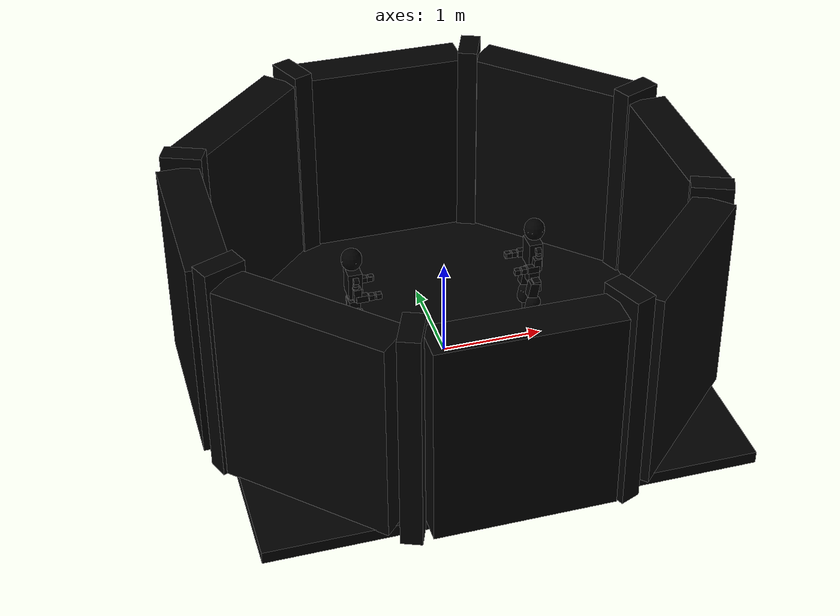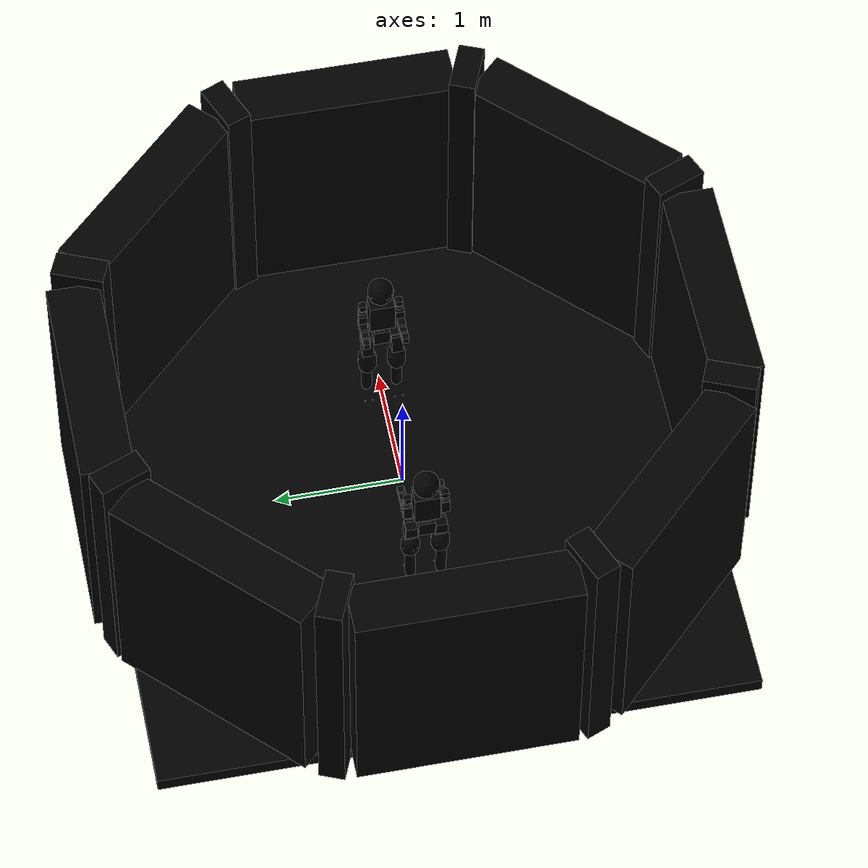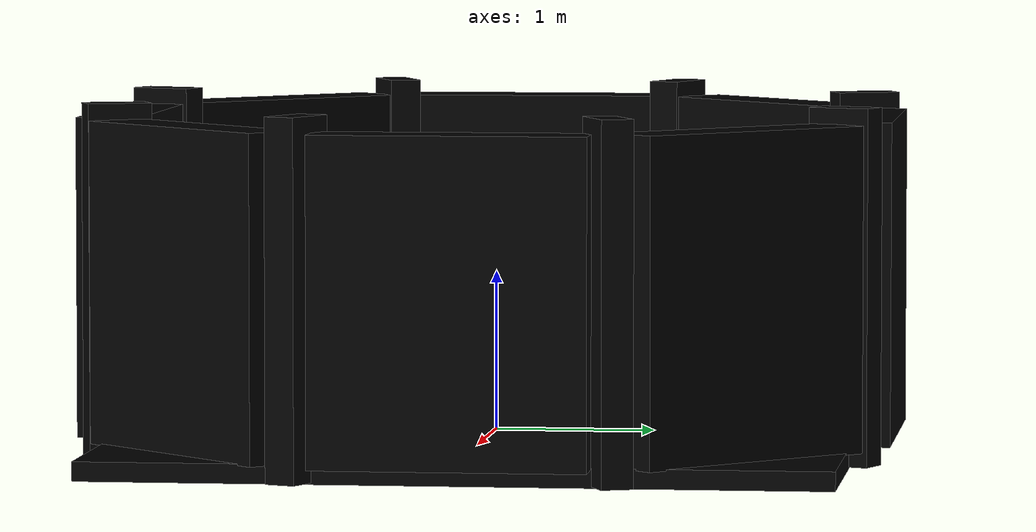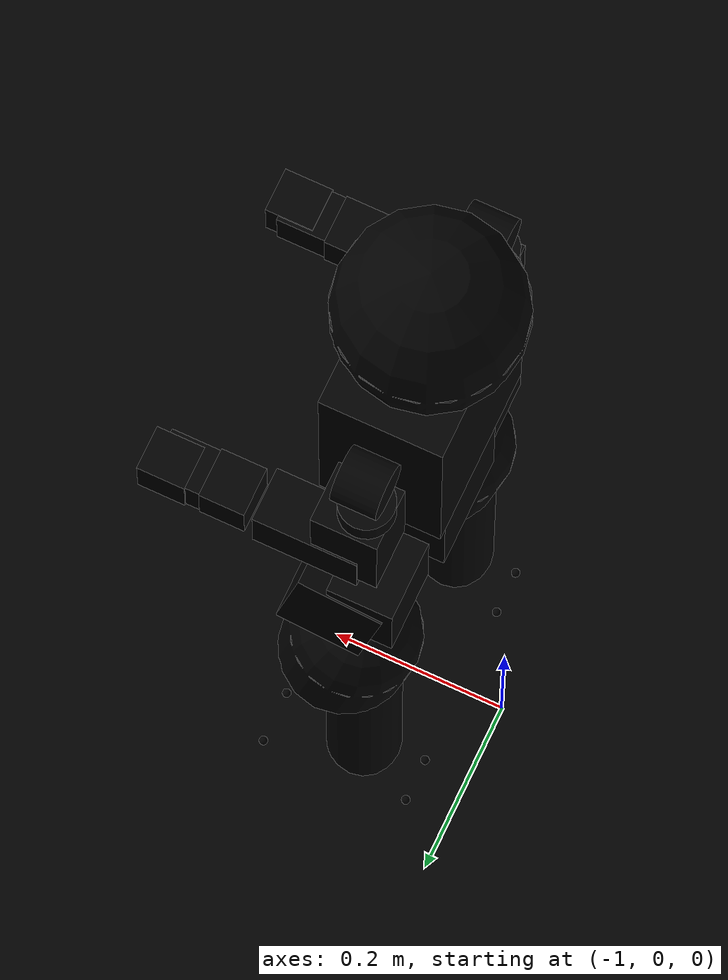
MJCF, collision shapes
<mujoco model="rek_g1_two_fighter_arena_reference">
  <compiler coordinate="local" />
  <option timestep="0.019999992913832199" gravity="0 0 -9.8100004196166992" impratio="1" magnetic="0 0 0" wind="0 0 0" density="0" viscosity="0" o_margin="0" o_solref="0.019999999552965164 1" o_solimp="0.89999997615814209 0.94999998807907104 0.0010000000474974513 0.5 2" integrator="implicitfast" cone="elliptic" jacobian="auto" solver="Newton" iterations="100" tolerance="9.9999999392252903e-09" noslip_iterations="0" noslip_tolerance="9.9999999747524271e-07" ccd_iterations="50" ccd_tolerance="9.9999999747524271e-07">
    <flag constraint="enable" equality="enable" frictionloss="enable" limit="enable" contact="enable" spring="enable" damper="enable" gravity="enable" clampctrl="enable" warmstart="enable" filterparent="enable" actuation="enable" refsafe="enable" override="disable" energy="disable" fwdinv="disable" multiccd="disable" />
  </option>
  <size memory="-1" />
  <custom />
  <worldbody>
    <geom name="arena_Collider_Floor_Rektagon" type="box" pos="0 0 -0.05000000074505806" quat="-0.70710678118654757 0 0 0.70710678118654757" size="2.2999999523162837 2.2999999523162837 0.059999998658895493" priority="0" contype="2" conaffinity="1" group="0" condim="3" solmix="1" solref="0.019999999552965164 1" solimp="0.89999997615814209 0.94999998807907104 0.0010000000474974513 0.5 2" margin="0" gap="0" friction="1 0.004999999888241291 9.9999997473787516e-05" fluidshape="none" fluidcoef="5 0.25 1.5 1 1" rgba="0 0 0 0" /><geom name="arena_Collider_Pillar_01" type="box" pos="2.2635049557696094 -0.93757428978008317 1" quat="-0.55557025832218543 0 0 0.83146959539589904" size="0.10000000149011609 0.20000000298023218 1.1000000238418579" priority="0" contype="2" conaffinity="1" group="0" condim="3" solmix="1" solref="0.019999999552965164 1" solimp="0.89999997615814209 0.94999998807907104 0.0010000000474974513 0.5 2" margin="0" gap="0" friction="1 0.004999999888241291 9.9999997473787516e-05" fluidshape="none" fluidcoef="5 0.25 1.5 1 1" rgba="0 0 0 0" /><geom name="arena_Collider_Pillar_02" type="box" pos="2.2635049557696085 0.93757428978008417 1" quat="-0.83146959539589904 0 0 0.55557025832218543" size="0.10000000149011609 0.20000000298023218 1.1000000238418579" priority="0" contype="2" conaffinity="1" group="0" condim="3" solmix="1" solref="0.019999999552965164 1" solimp="0.89999997615814209 0.94999998807907104 0.0010000000474974513 0.5 2" margin="0" gap="0" friction="1 0.004999999888241291 9.9999997473787516e-05" fluidshape="none" fluidcoef="5 0.25 1.5 1 1" rgba="0 0 0 0" /><geom name="arena_Collider_Pillar_03" type="box" pos="0.93757486498700593 2.2635047175110561 1" quat="-0.98078526155165546 0 0 0.19509041678937211" size="0.10000000149011611 0.20000000298023221 1.1000000238418579" priority="0" contype="2" conaffinity="1" group="0" condim="3" solmix="1" solref="0.019999999552965164 1" solimp="0.89999997615814209 0.94999998807907104 0.0010000000474974513 0.5 2" margin="0" gap="0" friction="1 0.004999999888241291 9.9999997473787516e-05" fluidshape="none" fluidcoef="5 0.25 1.5 1 1" rgba="0 0 0 0" /><geom name="arena_Collider_Pillar_04" type="box" pos="-0.93757449072096111 2.263504872537176 1" quat="-0.98078527768055968 0 0 -0.1950903357039187" size="0.10000000149011609 0.20000000298023218 1.1000000238418579" priority="0" contype="2" conaffinity="1" group="0" condim="3" solmix="1" solref="0.019999999552965164 1" solimp="0.89999997615814209 0.94999998807907104 0.0010000000474974513 0.5 2" margin="0" gap="0" friction="1 0.004999999888241291 9.9999997473787516e-05" fluidshape="none" fluidcoef="5 0.25 1.5 1 1" rgba="0 0 0 0" /><geom name="arena_Collider_Pillar_05" type="box" pos="-2.263504802540059 0.93757465970891984 1" quat="-0.83146964079483965 0 0 -0.55557019037786803" size="0.10000000149011609 0.20000000298023218 1.1000000238418579" priority="0" contype="2" conaffinity="1" group="0" condim="3" solmix="1" solref="0.019999999552965164 1" solimp="0.89999997615814209 0.94999998807907104 0.0010000000474974513 0.5 2" margin="0" gap="0" friction="1 0.004999999888241291 9.9999997473787516e-05" fluidshape="none" fluidcoef="5 0.25 1.5 1 1" rgba="0 0 0 0" /><geom name="arena_Collider_Pillar_06" type="box" pos="-2.2635049557696094 -0.93757428978008417 1" quat="-0.55557025832218543 0 0 -0.83146959539589904" size="0.10000000149011612 0.20000000298023224 1.1000000238418579" priority="0" contype="2" conaffinity="1" group="0" condim="3" solmix="1" solref="0.019999999552965164 1" solimp="0.89999997615814209 0.94999998807907104 0.0010000000474974513 0.5 2" margin="0" gap="0" friction="1 0.004999999888241291 9.9999997473787516e-05" fluidshape="none" fluidcoef="5 0.25 1.5 1 1" rgba="0 0 0 0" /><geom name="arena_Collider_Pillar_07" type="box" pos="-0.93757546360911292 -2.2635044695534319 1" quat="-0.19509054648200319 0 0 -0.98078523575416532" size="0.10000000149011609 0.20000000298023218 1.1000000238418579" priority="0" contype="2" conaffinity="1" group="0" condim="3" solmix="1" solref="0.019999999552965164 1" solimp="0.89999997615814209 0.94999998807907104 0.0010000000474974513 0.5 2" margin="0" gap="0" friction="1 0.004999999888241291 9.9999997473787516e-05" fluidshape="none" fluidcoef="5 0.25 1.5 1 1" rgba="0 0 0 0" /><geom name="arena_Collider_Pillar_08" type="box" pos="0.93757486498700704 -2.2635047175110556 1" quat="0.19509041678937211 0 0 -0.98078526155165546" size="0.10000000149011609 0.20000000298023218 1.1000000238418579" priority="0" contype="2" conaffinity="1" group="0" condim="3" solmix="1" solref="0.019999999552965164 1" solimp="0.89999997615814209 0.94999998807907104 0.0010000000474974513 0.5 2" margin="0" gap="0" friction="1 0.004999999888241291 9.9999997473787516e-05" fluidshape="none" fluidcoef="5 0.25 1.5 1 1" rgba="0 0 0 0" /><geom name="arena_Collider_Wall_01" type="box" pos="2.3399999141693111 5.1958435646633195e-16 1" quat="-0.70710678118654757 0 0 0.70710678118654757" size="0.83999997377395608 0.20000000298023218 1" priority="0" contype="2" conaffinity="1" group="0" condim="3" solmix="1" solref="0.019999999552965164 1" solimp="0.89999997615814209 0.94999998807907104 0.0010000000474974513 0.5 2" margin="0" gap="0" friction="1 0.004999999888241291 9.9999997473787516e-05" fluidshape="none" fluidcoef="5 0.25 1.5 1 1" rgba="0 0 0 0" /><geom name="arena_Collider_Wall_02" type="box" pos="1.6546306547274046 1.6546289598422794 1" quat="-0.92387943451283194 0 0 0.38268366895420286" size="0.83999997377395608 0.20000000298023218 1" priority="0" contype="2" conaffinity="1" group="0" condim="3" solmix="1" solref="0.019999999552965164 1" solimp="0.89999997615814209 0.94999998807907104 0.0010000000474974513 0.5 2" margin="0" gap="0" friction="1 0.004999999888241291 9.9999997473787516e-05" fluidshape="none" fluidcoef="5 0.25 1.5 1 1" rgba="0 0 0 0" /><geom name="arena_Collider_Wall_03" type="box" pos="1.1834834827893186e-06 2.3399999141690113 1" quat="-0.99999999999996803 0 0 2.5288109539722825e-07" size="0.83999997377395597 0.20000000298023218 1" priority="0" contype="2" conaffinity="1" group="0" condim="3" solmix="1" solref="0.019999999552965164 1" solimp="0.89999997615814209 0.94999998807907104 0.0010000000474974513 0.5 2" margin="0" gap="0" friction="1 0.004999999888241291 9.9999997473787516e-05" fluidshape="none" fluidcoef="5 0.25 1.5 1 1" rgba="0 0 0 0" /><geom name="arena_Collider_Wall_04" type="box" pos="-1.6546288949328962 1.6546307196367194 1" quat="-0.92387963801580608 0 0 -0.3826831776545489" size="0.8399999737739563 0.20000000298023224 1" priority="0" contype="2" conaffinity="1" group="0" condim="3" solmix="1" solref="0.019999999552965164 1" solimp="0.89999997615814209 0.94999998807907104 0.0010000000474974513 0.5 2" margin="0" gap="0" friction="1 0.004999999888241291 9.9999997473787516e-05" fluidshape="none" fluidcoef="5 0.25 1.5 1 1" rgba="0 0 0 0" /><geom name="arena_Collider_Wall_05" type="box" pos="-2.3399999141681804 2.3013349838180236e-06 1" quat="-0.70710712889792215 0 0 -0.70710643347500202" size="0.83999997377395652 0.20000000298023229 1" priority="0" contype="2" conaffinity="1" group="0" condim="3" solmix="1" solref="0.019999999552965164 1" solimp="0.89999997615814209 0.94999998807907104 0.0010000000474974513 0.5 2" margin="0" gap="0" friction="1 0.004999999888241291 9.9999997473787516e-05" fluidshape="none" fluidcoef="5 0.25 1.5 1 1" rgba="0 0 0 0" /><geom name="arena_Collider_Wall_06" type="box" pos="-1.6546316413733664 -1.6546279731947187 1" quat="-0.38268394440632869 0 0 -0.92387932041669496" size="0.83999997377395608 0.20000000298023218 1" priority="0" contype="2" conaffinity="1" group="0" condim="3" solmix="1" solref="0.019999999552965164 1" solimp="0.89999997615814209 0.94999998807907104 0.0010000000474974513 0.5 2" margin="0" gap="0" friction="1 0.004999999888241291 9.9999997473787516e-05" fluidshape="none" fluidcoef="5 0.25 1.5 1 1" rgba="0 0 0 0" /><geom name="arena_Collider_Wall_07" type="box" pos="-3.7476975373293713e-06 -2.3399999141663095 1" quat="-8.0079010156275388e-07 0 0 -0.99999999999967937" size="0.83999997377395597 0.20000000298023218 1" priority="0" contype="2" conaffinity="1" group="0" condim="3" solmix="1" solref="0.019999999552965164 1" solimp="0.89999997615814209 0.94999998807907104 0.0010000000474974513 0.5 2" margin="0" gap="0" friction="1 0.004999999888241291 9.9999997473787516e-05" fluidshape="none" fluidcoef="5 0.25 1.5 1 1" rgba="0 0 0 0" /><geom name="arena_Collider_Wall_08" type="box" pos="1.6546254351887162 -1.6546341793698496 1" quat="0.38268221176393891 0 0 -0.92388003809989316" size="0.8399999737739563 0.20000000298023224 1" priority="0" contype="2" conaffinity="1" group="0" condim="3" solmix="1" solref="0.019999999552965164 1" solimp="0.89999997615814209 0.94999998807907104 0.0010000000474974513 0.5 2" margin="0" gap="0" friction="1 0.004999999888241291 9.9999997473787516e-05" fluidshape="none" fluidcoef="5 0.25 1.5 1 1" rgba="0 0 0 0" /><body name="arena_spawn_reference__player" pos="-0.90000003576278687 0 0.0099999997764825821" quat="-0.99999999999988631 0 0 4.7683710135965193e-07" /><body name="arena_spawn_reference__opponent" pos="0.89999997615814209 0 0.0099999997764825821" quat="1.1026858146572184e-06 0 0 -0.99999999999939204" /><body name="player__pelvis_3266" pos="-0.90000003576278687 0 0.80299998261034489" quat="0.99999999999988631 0 0 -4.7683710135965193e-07" gravcomp="0">
      <body name="player__left_hip_pitch_link_3457" pos="-1.3877787807814457e-17 0.064451999962329781 -0.10270000249147415" quat="1 0 0 0" gravcomp="0">
        <body name="player__left_hip_roll_link_3425" pos="9.7144514654701197e-17 0.052000001072883786 -0.030464999377727509" quat="0.99617868596660997 0 -0.087338568947737019 -1.1102230246251565e-16" gravcomp="0">
          <body name="player__left_hip_yaw_link_2943" pos="0.025001000612975076 1.5543122344752192e-15 -0.12411999702453594" quat="1 0 0 -1.2576745200831851e-17" gravcomp="0">
            <body name="player__left_knee_link_3106" pos="-0.078272998332977878 0.0021488999482234955 -0.17734000086784374" quat="0.99617868596660997 6.9388939039072284e-18 0.087338568947737005 -6.1259230688899764e-19" gravcomp="0">
              <body name="player__left_ankle_pitch_link_3033" pos="1.4934884925987824e-16 -9.4445000285932839e-05 -0.30000999569892883" quat="1 0 0 9.6296497219361793e-35" gravcomp="0">
                <body name="player__left_ankle_roll_link_3045" pos="-2.9735684393186275e-19 -4.565577275908913e-19 -0.01755799911916256" quat="1 0 0 9.6296497219361793e-35" gravcomp="0">
                  <inertial pos="0.026505000889301987 1.2490009027033011e-15 -0.016425000503659248" quat="-0.00048109179920679656 0.72848180059747192 -0.00061896679591005453 0.68506470616216375" mass="0.60799998044967651" diaginertia="0.00167218002025038 0.0016160999657586217 0.00021762099640909582" />
                  <joint name="player__joint__left_ankle_roll_joint_2905" type="hinge" pos="0 0 0" axis="1 1.9259299443872359e-34 0" armature="0.0072194500826299191" springref="0" springdamper="0 0" damping="0.05000000074505806" stiffness="0" solreflimit="0.019999999552965164 1" solimplimit="0.89999997615814209 0.94999998807907104 0.0010000000474974513 0.5 2" solreffriction="0.019999999552965164 1" solimpfriction="0.89999997615814209 0.94999998807907104 0.0010000000474974513 0.5 2" frictionloss="0.20000000298023224" limited="true" margin="0" range="-15.000034332275391 15.000034332275391" ref="0" />
                  <geom name="player__mjgeom_authored_3078" density="0" type="sphere" size="0.004999999888241291" pos="-0.050000000745058351 0.025000000372528544 -0.029999999329447746" quat="1 0 0 9.6296497219361793e-35" priority="0" contype="5" conaffinity="9" group="0" condim="3" solmix="1" solref="0.019999999552965164 1" solimp="0.89999997615814209 0.94999998807907104 0.0010000000474974513" margin="0" gap="0" friction="1 0.004999999888241291 9.9999997473787516e-05" fluidshape="none" fluidcoef="5 0.25 1.5 1 1" rgba="0 0 0 0" />
                  <geom name="player__mjgeom_authored_3434" density="0" type="sphere" size="0.004999999888241291" pos="-0.050000000745058004 -0.02500000037252894 -0.029999999329447746" quat="1 0 0 9.6296497219361793e-35" priority="0" contype="5" conaffinity="9" group="0" condim="3" solmix="1" solref="0.019999999552965164 1" solimp="0.89999997615814209 0.94999998807907104 0.0010000000474974513" margin="0" gap="0" friction="1 0.004999999888241291 9.9999997473787516e-05" fluidshape="none" fluidcoef="5 0.25 1.5 1 1" rgba="0 0 0 0" />
                  <geom name="player__mjgeom_authored_3201" density="0" type="sphere" size="0.004999999888241291" pos="0.11999999731779078 0.029999999329447302 -0.02999999932944775" quat="1 0 0 9.6296497219361793e-35" priority="0" contype="5" conaffinity="9" group="0" condim="3" solmix="1" solref="0.019999999552965164 1" solimp="0.89999997615814209 0.94999998807907104 0.0010000000474974513" margin="0" gap="0" friction="1 0.004999999888241291 9.9999997473787516e-05" fluidshape="none" fluidcoef="5 0.25 1.5 1 1" rgba="0 0 0 0" />
                  <geom name="player__mjgeom_authored_3130" density="0" type="sphere" size="0.004999999888241291" pos="0.11999999731779179 -0.029999999329446275 -0.02999999932944775" quat="1 0 0 9.6296497219361793e-35" priority="0" contype="5" conaffinity="9" group="0" condim="3" solmix="1" solref="0.019999999552965164 1" solimp="0.89999997615814209 0.94999998807907104 0.0010000000474974513" margin="0" gap="0" friction="1 0.004999999888241291 9.9999997473787516e-05" fluidshape="none" fluidcoef="5 0.25 1.5 1 1" rgba="0 0 0 0" />
                <geom name="official_0_player__left_ankle_roll_link_3045" type="mesh" mesh="official_0" contype="0" conaffinity="0" group="2" mass="0" material="mat_0" /></body>
                <inertial pos="-0.0072690001688901209 -6.1582683397176652e-16 0.011137000285089016" quat="0.60305298197600943 0.3692250004128147 0.3692250004128147 0.60305298197600932" mass="0.074000000953674316" diaginertia="1.8900000213761814e-05 1.4080499568080995e-05 6.919499810464913e-06" />
                <joint name="player__joint__left_ankle_pitch_joint_2982" type="hinge" pos="0 0 0" axis="-2.2204460492503126e-16 1 6.5368229940789346e-33" armature="0.0072194500826299191" springref="0" springdamper="0 0" damping="0.05000000074505806" stiffness="0" solreflimit="0.019999999552965164 1" solimplimit="0.89999997615814209 0.94999998807907104 0.0010000000474974513 0.5 2" solreffriction="0.019999999552965164 1" solimpfriction="0.89999997615814209 0.94999998807907104 0.0010000000474974513 0.5 2" frictionloss="0.20000000298023224" limited="true" margin="0" range="-50.000308990478516 30.000068664550781" ref="0" />
                <geom name="player__mjgeom_3039" density="0" type="box" size="0.013479510380420836 0.016846910875756297 0.0059266640164423725" pos="-0.0035227723419665718 0.00014300439215739029 -0.0058391094207763672" quat="2.9802318610457207e-08 2.980231861541685e-08 -0.70710678118654691 -0.70710678118654691" priority="0" contype="5" conaffinity="10" group="0" condim="3" solmix="1" solref="0.019999999552965164 1" solimp="0.89999997615814209 0.94999998807907104 0.0010000000474974513" margin="0" gap="0" friction="1 0.004999999888241291 9.9999997473787516e-05" fluidshape="none" fluidcoef="5 0.25 1.5 1 1" rgba="0 0 0 0" />
              <geom name="official_1_player__left_ankle_pitch_link_3033" type="mesh" mesh="official_1" contype="0" conaffinity="0" group="2" mass="0" material="mat_0" /></body>
              <inertial pos="0.0054569998756053761 0.0039639999158684758 -0.12073999643325806" quat="0.92341787234595951 -0.032769897917134708 0.015824598274911447 0.38206694297203919" mass="1.9320000410079956" diaginertia="0.011380399577319622 0.011277800425887108 0.0014645799528807402" />
              <joint name="player__joint__left_knee_joint_3137" type="hinge" pos="0 0 0" axis="-2.2204460492503126e-16 1 6.5368229940789346e-33" armature="0.025101924315094948" springref="0" springdamper="0 0" damping="0.05000000074505806" stiffness="0" solreflimit="0.019999999552965164 1" solimplimit="0.89999997615814209 0.94999998807907104 0.0010000000474974513 0.5 2" solreffriction="0.019999999552965164 1" solimpfriction="0.89999997615814209 0.94999998807907104 0.0010000000474974513 0.5 2" frictionloss="0.20000000298023224" limited="true" margin="0" range="-5.000030517578125 165.00039672851562" ref="0" />
              <geom name="player__mjgeom_3224" density="0" type="capsule" size="0.041472329758107669 0.13606720604002479" pos="0.011999648064374422 -8.3323335275985524e-05 -0.13741210103034973" quat="4.2146847789581443e-08 1.5407439555097887e-33 7.7037197775489434e-34 -0.99999999999999922" priority="0" contype="5" conaffinity="10" group="0" condim="3" solmix="1" solref="0.019999999552965164 1" solimp="0.89999997615814209 0.94999998807907104 0.0010000000474974513" margin="0" gap="0" friction="1 0.004999999888241291 9.9999997473787516e-05" fluidshape="none" fluidcoef="5 0.25 1.5 1 1" rgba="0 0 0 0" />
            <geom name="official_2_player__left_knee_link_3106" type="mesh" mesh="official_2" contype="0" conaffinity="0" group="2" mass="0" material="mat_0" /></body>
            <inertial pos="-0.057709001004695545 -0.010981000028549924 -0.15078000724315654" quat="0.60059793208355583 0.15831996789768774 0.22348195109437591 0.75118088985069531" mass="1.7020000219345093" diaginertia="0.0077616600319743156 0.0071757500991225243 0.0016013899585232139" />
            <joint name="player__joint__left_hip_yaw_joint_3267" type="hinge" pos="0 0 0" axis="-2.2204460492503131e-16 1.3247655120144351e-16 1" armature="0.010177520103752613" springref="0" springdamper="0 0" damping="0.05000000074505806" stiffness="0" solreflimit="0.019999999552965164 1" solimplimit="0.89999997615814209 0.94999998807907104 0.0010000000474974513 0.5 2" solreffriction="0.019999999552965164 1" solimpfriction="0.89999997615814209 0.94999998807907104 0.0010000000474974513 0.5 2" frictionloss="0.20000000298023224" limited="true" margin="0" range="-157.99884033203125 157.99884033203125" ref="0" />
            <geom name="player__mjgeom_3399" density="0" type="capsule" size="0.071829627268016338 0.041044317185878761" pos="-0.037462260574102665 -0.0010485649108891298 -0.11335682868957533" quat="4.1985788967052733e-08 2.9951634505920302e-09 -6.9388939039072268e-18 -0.99999999999999911" priority="0" contype="5" conaffinity="10" group="0" condim="3" solmix="1" solref="0.019999999552965164 1" solimp="0.89999997615814209 0.94999998807907104 0.0010000000474974513" margin="0" gap="0" friction="1 0.004999999888241291 9.9999997473787516e-05" fluidshape="none" fluidcoef="5 0.25 1.5 1 1" rgba="0 0 0 0" />
          <geom name="official_3_player__left_hip_yaw_link_2943" type="mesh" mesh="official_3" contype="0" conaffinity="0" group="2" mass="0" material="mat_0" /></body>
          <inertial pos="0.029812000691890293 -0.0010450000409044022 -0.087934002280235485" quat="0.97780777106336325 -1.9711895438305482e-05 0.20557596017013183 -0.040379289984682841" mass="1.5199999809265137" diaginertia="0.0025498599279671907 0.0024116900749504566 0.0014875499764457345" />
          <joint name="player__joint__left_hip_roll_joint_3248" type="hinge" pos="0 0 0" axis="1 -2.5153490401663703e-17 0" armature="0.025101924315094948" springref="0" springdamper="0 0" damping="0.05000000074505806" stiffness="0" solreflimit="0.019999999552965164 1" solimplimit="0.89999997615814209 0.94999998807907104 0.0010000000474974513 0.5 2" solreffriction="0.019999999552965164 1" solimpfriction="0.89999997615814209 0.94999998807907104 0.0010000000474974513 0.5 2" frictionloss="0.20000000298023224" limited="true" margin="0" range="-30.000068664550781 170.00230407714844" ref="0" />
          <geom name="player__mjgeom_3141" density="0" type="box" size="0.047961223754100502 0.076655694283545031 0.044093289761804037" pos="0.026883890852332802 -0.0001681223511682331 -0.038719426840544219" quat="2.7570534225432319e-08 3.1806334954698201e-08 -0.70710678118654702 -0.70710678118654691" priority="0" contype="5" conaffinity="10" group="0" condim="3" solmix="1" solref="0.019999999552965164 1" solimp="0.89999997615814209 0.94999998807907104 0.0010000000474974513" margin="0" gap="0" friction="1 0.004999999888241291 9.9999997473787516e-05" fluidshape="none" fluidcoef="5 0.25 1.5 1 1" rgba="0 0 0 0" />
        <geom name="official_4_player__left_hip_roll_link_3425" type="mesh" mesh="official_4" contype="0" conaffinity="0" group="2" mass="0" material="mat_0" /></body>
        <inertial pos="0.0027409999165692034 0.04779100045561932 -0.026060000061988831" quat="0.95486247817542302 0.29396413007377181 0.030255613910682867 0.030122015695304819" mass="1.3500000238418579" diaginertia="0.0018151700496673584 0.0015342199476435781 0.0011621200246736407" />
        <joint name="player__joint__left_hip_pitch_joint_3047" type="hinge" pos="0 0 0" axis="-2.2204460492503126e-16 1 0" armature="0.010177520103752613" springref="0" springdamper="0 0" damping="0.05000000074505806" stiffness="0" solreflimit="0.019999999552965164 1" solimplimit="0.89999997615814209 0.94999998807907104 0.0010000000474974513 0.5 2" solreffriction="0.019999999552965164 1" solimpfriction="0.89999997615814209 0.94999998807907104 0.0010000000474974513 0.5 2" frictionloss="0.20000000298023224" limited="true" margin="0" range="-144.99842834472656 165.00039672851562" ref="0" />
        <geom name="player__mjgeom_3337" density="0" type="box" size="0.037135550519451506 0.05274748546071352 0.044440440251491964" pos="-0.001050249789842167 0.04937807470559951 -0.021436683833599091" quat="3.0908621106995326e-08 3.0908621106995326e-08 -0.70710678118654691 -0.70710678118654691" priority="0" contype="5" conaffinity="10" group="0" condim="3" solmix="1" solref="0.019999999552965164 1" solimp="0.89999997615814209 0.94999998807907104 0.0010000000474974513" margin="0" gap="0" friction="1 0.004999999888241291 9.9999997473787516e-05" fluidshape="none" fluidcoef="5 0.25 1.5 1 1" rgba="0 0 0 0" />
      <geom name="official_5_player__left_hip_pitch_link_3457" type="mesh" mesh="official_5" contype="0" conaffinity="0" group="2" mass="0" material="mat_0" /></body>
      <body name="player__right_hip_pitch_link_3469" pos="1.3877787807814457e-17 -0.064451999962329781 -0.10270000249147415" quat="1 0 0 0" gravcomp="0">
        <body name="player__right_hip_roll_link_3345" pos="-9.7144514654701197e-17 -0.052000001072883786 -0.030464999377727509" quat="0.99617868596660997 0 -0.087338568947737019 -1.1102230246251565e-16" gravcomp="0">
          <body name="player__right_hip_yaw_link_3191" pos="0.025001000612975076 1.5543122344752192e-15 -0.12411999702453594" quat="1 0 0 -1.2576745200831851e-17" gravcomp="0">
            <body name="player__right_knee_link_3429" pos="-0.078272998332977572 -0.0021488999482247723 -0.17734000086784379" quat="0.99617868596660997 6.9388939039072284e-18 0.087338568947737005 -6.1259230688899764e-19" gravcomp="0">
              <body name="player__right_ankle_pitch_link_3173" pos="-1.5951324462692984e-16 9.444500028591724e-05 -0.30000999569892883" quat="1 0 0 9.6296497219361793e-35" gravcomp="0">
                <body name="player__right_ankle_roll_link_3090" pos="-2.9735684393186275e-19 -4.565577275908913e-19 -0.01755799911916256" quat="1 0 0 9.6296497219361793e-35" gravcomp="0">
                  <inertial pos="0.026505000889301987 1.2490009027033011e-15 -0.016425000503659248" quat="0.00048109179920674972 0.72848180059747181 0.00061896679591011828 0.68506470616216364" mass="0.60799998044967651" diaginertia="0.00167218002025038 0.0016160999657586217 0.00021762099640909582" />
                  <joint name="player__joint__right_ankle_roll_joint_3474" type="hinge" pos="0 0 0" axis="1 1.9259299443872359e-34 0" armature="0.0072194500826299191" springref="0" springdamper="0 0" damping="0.05000000074505806" stiffness="0" solreflimit="0.019999999552965164 1" solimplimit="0.89999997615814209 0.94999998807907104 0.0010000000474974513 0.5 2" solreffriction="0.019999999552965164 1" solimpfriction="0.89999997615814209 0.94999998807907104 0.0010000000474974513 0.5 2" frictionloss="0.20000000298023224" limited="true" margin="0" range="-15.000034332275391 15.000034332275391" ref="0" />
                  <geom name="player__mjgeom_authored_3138" density="0" type="sphere" size="0.004999999888241291" pos="-0.050000000745058351 0.025000000372528544 -0.029999999329447746" quat="1 0 0 9.6296497219361793e-35" priority="0" contype="5" conaffinity="9" group="0" condim="3" solmix="1" solref="0.019999999552965164 1" solimp="0.89999997615814209 0.94999998807907104 0.0010000000474974513" margin="0" gap="0" friction="1 0.004999999888241291 9.9999997473787516e-05" fluidshape="none" fluidcoef="5 0.25 1.5 1 1" rgba="0 0 0 0" />
                  <geom name="player__mjgeom_authored_3263" density="0" type="sphere" size="0.004999999888241291" pos="-0.050000000745058004 -0.02500000037252894 -0.029999999329447746" quat="1 0 0 9.6296497219361793e-35" priority="0" contype="5" conaffinity="9" group="0" condim="3" solmix="1" solref="0.019999999552965164 1" solimp="0.89999997615814209 0.94999998807907104 0.0010000000474974513" margin="0" gap="0" friction="1 0.004999999888241291 9.9999997473787516e-05" fluidshape="none" fluidcoef="5 0.25 1.5 1 1" rgba="0 0 0 0" />
                  <geom name="player__mjgeom_authored_3316" density="0" type="sphere" size="0.004999999888241291" pos="0.11999999731779072 0.029999999329447358 -0.02999999932944775" quat="1 0 0 9.6296497219361793e-35" priority="0" contype="5" conaffinity="9" group="0" condim="3" solmix="1" solref="0.019999999552965164 1" solimp="0.89999997615814209 0.94999998807907104 0.0010000000474974513" margin="0" gap="0" friction="1 0.004999999888241291 9.9999997473787516e-05" fluidshape="none" fluidcoef="5 0.25 1.5 1 1" rgba="0 0 0 0" />
                  <geom name="player__mjgeom_authored_3217" density="0" type="sphere" size="0.004999999888241291" pos="0.11999999731779183 -0.029999999329446303 -0.02999999932944775" quat="1 0 0 9.6296497219361793e-35" priority="0" contype="5" conaffinity="9" group="0" condim="3" solmix="1" solref="0.019999999552965164 1" solimp="0.89999997615814209 0.94999998807907104 0.0010000000474974513" margin="0" gap="0" friction="1 0.004999999888241291 9.9999997473787516e-05" fluidshape="none" fluidcoef="5 0.25 1.5 1 1" rgba="0 0 0 0" />
                <geom name="official_6_player__right_ankle_roll_link_3090" type="mesh" mesh="official_6" contype="0" conaffinity="0" group="2" mass="0" material="mat_0" /></body>
                <inertial pos="-0.0072690001688901209 -6.1582683397176652e-16 0.011137000285089016" quat="0.60305298197600943 0.3692250004128147 0.3692250004128147 0.60305298197600932" mass="0.074000000953674316" diaginertia="1.8900000213761814e-05 1.4080499568080995e-05 6.919499810464913e-06" />
                <joint name="player__joint__right_ankle_pitch_joint_3312" type="hinge" pos="0 0 0" axis="-2.2204460492503126e-16 1 6.5368229940789346e-33" armature="0.0072194500826299191" springref="0" springdamper="0 0" damping="0.05000000074505806" stiffness="0" solreflimit="0.019999999552965164 1" solimplimit="0.89999997615814209 0.94999998807907104 0.0010000000474974513 0.5 2" solreffriction="0.019999999552965164 1" solimpfriction="0.89999997615814209 0.94999998807907104 0.0010000000474974513 0.5 2" frictionloss="0.20000000298023224" limited="true" margin="0" range="-50.000308990478516 30.000068664550781" ref="0" />
                <geom name="player__mjgeom_3271" density="0" type="box" size="0.013479510380420836 0.016846909420564774 0.005926662197452969" pos="-0.0035228133201594962 -0.00014299694157599973 -0.0058391094207763672" quat="2.9802318610457207e-08 2.980231861541685e-08 -0.70710678118654691 -0.70710678118654691" priority="0" contype="5" conaffinity="10" group="0" condim="3" solmix="1" solref="0.019999999552965164 1" solimp="0.89999997615814209 0.94999998807907104 0.0010000000474974513" margin="0" gap="0" friction="1 0.004999999888241291 9.9999997473787516e-05" fluidshape="none" fluidcoef="5 0.25 1.5 1 1" rgba="0 0 0 0" />
              <geom name="official_7_player__right_ankle_pitch_link_3173" type="mesh" mesh="official_7" contype="0" conaffinity="0" group="2" mass="0" material="mat_0" /></body>
              <inertial pos="0.0054569998756047039 -0.003963999915868782 -0.12073999643325806" quat="0.92343889150208058 0.034527595519145943 0.011633299100056282 -0.38201194374145381" mass="1.9320000410079956" diaginertia="0.011374000459909439 0.011284300126135349 0.0014645199989899993" />
              <joint name="player__joint__right_knee_joint_3412" type="hinge" pos="0 0 0" axis="-2.2204460492503126e-16 1 6.5368229940789346e-33" armature="0.025101924315094948" springref="0" springdamper="0 0" damping="0.05000000074505806" stiffness="0" solreflimit="0.019999999552965164 1" solimplimit="0.89999997615814209 0.94999998807907104 0.0010000000474974513 0.5 2" solreffriction="0.019999999552965164 1" solimpfriction="0.89999997615814209 0.94999998807907104 0.0010000000474974513 0.5 2" frictionloss="0.20000000298023224" limited="true" margin="0" range="-5.000030517578125 165.00039672851562" ref="0" />
              <geom name="player__mjgeom_3023" density="0" type="capsule" size="0.041472326847724623 0.1360671943984926" pos="0.011999662965535526 8.3368038757580809e-05 -0.13741210103034973" quat="4.2146847789581443e-08 1.5407439555097887e-33 7.7037197775489434e-34 -0.99999999999999922" priority="0" contype="5" conaffinity="10" group="0" condim="3" solmix="1" solref="0.019999999552965164 1" solimp="0.89999997615814209 0.94999998807907104 0.0010000000474974513" margin="0" gap="0" friction="1 0.004999999888241291 9.9999997473787516e-05" fluidshape="none" fluidcoef="5 0.25 1.5 1 1" rgba="0 0 0 0" />
            <geom name="official_8_player__right_knee_link_3429" type="mesh" mesh="official_8" contype="0" conaffinity="0" group="2" mass="0" material="mat_0" /></body>
            <inertial pos="-0.057709001004695989 0.010981000028550493 -0.15078000724315646" quat="0.7511808898506952 0.22348195109437591 0.15831996789768774 0.60059793208355594" mass="1.7020000219345093" diaginertia="0.0077616600319743156 0.0071757500991225243 0.0016013899585232139" />
            <joint name="player__joint__right_hip_yaw_joint_3071" type="hinge" pos="0 0 0" axis="-2.2204460492503131e-16 1.3247655120144351e-16 1" armature="0.010177520103752613" springref="0" springdamper="0 0" damping="0.05000000074505806" stiffness="0" solreflimit="0.019999999552965164 1" solimplimit="0.89999997615814209 0.94999998807907104 0.0010000000474974513 0.5 2" solreffriction="0.019999999552965164 1" solimpfriction="0.89999997615814209 0.94999998807907104 0.0010000000474974513 0.5 2" frictionloss="0.20000000298023224" limited="true" margin="0" range="-157.99884033203125 157.99884033203125" ref="0" />
            <geom name="player__mjgeom_3406" density="0" type="capsule" size="0.071829644730314612 0.041044323006644852" pos="-0.037462309002875629 0.0010465979576122011 -0.11335794627666473" quat="4.1985788967052733e-08 2.9951634505920302e-09 -6.9388939039072268e-18 -0.99999999999999911" priority="0" contype="5" conaffinity="10" group="0" condim="3" solmix="1" solref="0.019999999552965164 1" solimp="0.89999997615814209 0.94999998807907104 0.0010000000474974513" margin="0" gap="0" friction="1 0.004999999888241291 9.9999997473787516e-05" fluidshape="none" fluidcoef="5 0.25 1.5 1 1" rgba="0 0 0 0" />
          <geom name="official_9_player__right_hip_yaw_link_3191" type="mesh" mesh="official_9" contype="0" conaffinity="0" group="2" mass="0" material="mat_0" /></body>
          <inertial pos="0.029812000691889974 0.0010450000409024038 -0.087934002280235443" quat="0.97780777106336314 1.9711895438333234e-05 0.20557596017013174 0.04037928998468273" mass="1.5199999809265137" diaginertia="0.0025498599279671907 0.0024116900749504566 0.0014875499764457345" />
          <joint name="player__joint__right_hip_roll_joint_3059" type="hinge" pos="0 0 0" axis="1 -2.5153490401663703e-17 0" armature="0.025101924315094948" springref="0" springdamper="0 0" damping="0.05000000074505806" stiffness="0" solreflimit="0.019999999552965164 1" solimplimit="0.89999997615814209 0.94999998807907104 0.0010000000474974513 0.5 2" solreffriction="0.019999999552965164 1" solimpfriction="0.89999997615814209 0.94999998807907104 0.0010000000474974513 0.5 2" frictionloss="0.20000000298023224" limited="true" margin="0" range="-170.00230407714844 30.000068664550781" ref="0" />
          <geom name="player__mjgeom_3062" density="0" type="box" size="0.04796121793333441 0.076655682642012848 0.044093283941037946" pos="0.026883879676461598 0.00016814470291211248 -0.038719426840544163" quat="2.7570534225432319e-08 3.1806334954698201e-08 -0.70710678118654702 -0.70710678118654691" priority="0" contype="5" conaffinity="10" group="0" condim="3" solmix="1" solref="0.019999999552965164 1" solimp="0.89999997615814209 0.94999998807907104 0.0010000000474974513" margin="0" gap="0" friction="1 0.004999999888241291 9.9999997473787516e-05" fluidshape="none" fluidcoef="5 0.25 1.5 1 1" rgba="0 0 0 0" />
        <geom name="official_10_player__right_hip_roll_link_3345" type="mesh" mesh="official_10" contype="0" conaffinity="0" group="2" mass="0" material="mat_0" /></body>
        <inertial pos="0.0027409999165676213 -0.047791000455619327 -0.026060000061988831" quat="0.95486247817542302 -0.29396413007377176 0.030255613910682905 -0.03012201569530476" mass="1.3500000238418579" diaginertia="0.0018151700496673584 0.0015342199476435781 0.0011621200246736407" />
        <joint name="player__joint__right_hip_pitch_joint_3298" type="hinge" pos="0 0 0" axis="-2.2204460492503126e-16 1 0" armature="0.010177520103752613" springref="0" springdamper="0 0" damping="0.05000000074505806" stiffness="0" solreflimit="0.019999999552965164 1" solimplimit="0.89999997615814209 0.94999998807907104 0.0010000000474974513 0.5 2" solreffriction="0.019999999552965164 1" solimpfriction="0.89999997615814209 0.94999998807907104 0.0010000000474974513 0.5 2" frictionloss="0.20000000298023224" limited="true" margin="0" range="-144.99842834472656 165.00039672851562" ref="0" />
        <geom name="player__mjgeom_3024" density="0" type="box" size="0.037135550519451506 0.05274748546071352 0.044440440251491964" pos="-0.0010502411751079771 -0.049378067255020773 -0.021436624228954315" quat="3.0908621106995326e-08 3.0908621106995326e-08 -0.70710678118654691 -0.70710678118654691" priority="0" contype="5" conaffinity="10" group="0" condim="3" solmix="1" solref="0.019999999552965164 1" solimp="0.89999997615814209 0.94999998807907104 0.0010000000474974513" margin="0" gap="0" friction="1 0.004999999888241291 9.9999997473787516e-05" fluidshape="none" fluidcoef="5 0.25 1.5 1 1" rgba="0 0 0 0" />
      <geom name="official_11_player__right_hip_pitch_link_3469" type="mesh" mesh="official_11" contype="0" conaffinity="0" group="2" mass="0" material="mat_0" /></body>
      <body name="player__waist_yaw_link_3359" pos="0 0 0" quat="1 0 0 0" gravcomp="0">
        <body name="player__waist_roll_link_2894" pos="-0.0039634997956447936 1.2281842209915794e-15 0.035000000149011612" quat="1 0 0 0" gravcomp="0">
          <body name="player__torso_link_3347" pos="0 0 0.018999999389052391" quat="1 0 0 0" gravcomp="0">
            <body name="player__left_shoulder_pitch_link_3161" pos="0.00395630020648155 0.10022000223398055 0.23778000473976135" quat="0.9902641388950898 0.1392010247334452 1.3872202005688061e-05 -9.8686814262172184e-05" gravcomp="0">
              <body name="player__left_shoulder_roll_link_3360" pos="-4.5796699765787707e-16 0.037999998778103894 -0.0138309998437765" quat="0.99026821913005192 -0.13917203088622282 0 6.3533823791176933e-18" gravcomp="0">
                <body name="player__left_shoulder_yaw_link_3168" pos="5.8460181140418399e-16 0.0062400000169883594 -0.10320000350475353" quat="1 0 0 -3.2819588146978036e-18" gravcomp="0">
                  <body name="player__left_elbow_link_3284" pos="0.015783000737429023 6.1756155744774333e-16 -0.0805179998278613" quat="1 0 0 -3.2819588146978036e-18" gravcomp="0">
                    <body name="player__left_wrist_roll_link_3032" pos="0.10000000149011658 0.0018879099516206088 -0.0099999997764823843" quat="1 0 0 -3.2819588146978036e-18" gravcomp="0">
                      <body name="player__left_wrist_pitch_link_2914" pos="0.037999998778104768 -1.3877787807814457e-17 1.3392692038921919e-16" quat="1 0 0 -3.2819588146978036e-18" gravcomp="0">
                        <body name="player__left_wrist_yaw_link_3467" pos="0.046000000089407536 9.7144514654701197e-16 -3.156917205405195e-16" quat="1 0 0 -3.2819588146978036e-18" gravcomp="0">
                          <inertial pos="0.070824399590491569 0.00019174499902747943 0.0016174199990922002" quat="0.51057085673791158 0.52629485922096653 0.46807784345838327 0.49318784846227443" mass="0.25457599759101868" diaginertia="0.00064611301058903337 0.00055999297183007002 0.00014756599557586014" />
                          <joint name="player__joint__left_wrist_yaw_joint_3398" type="hinge" pos="0 0 0" axis="-4.4408920985006252e-16 -6.0488425288159066e-17 1" armature="0.0042500002309679985" springref="0" springdamper="0 0" damping="0.05000000074505806" stiffness="0" solreflimit="0.019999999552965164 1" solimplimit="0.89999997615814209 0.94999998807907104 0.0010000000474974513 0.5 2" solreffriction="0.019999999552965164 1" solimpfriction="0.89999997615814209 0.94999998807907104 0.0010000000474974513 0.5 2" frictionloss="0.10000000149011612" limited="true" margin="0" range="-0.0099999997764825821 0.0099999997764825821" ref="0" />
                          <geom name="player__mjgeom_3001" density="0" type="box" size="0.02654675918165595 0.027197948656976226 0.024242402287200097" pos="0.011494085192680591 0.0030774502083663752 -0.0002476256340736681" quat="3.0904894321660931e-08 3.0899774882994809e-08 -0.70710678118654691 -0.70710678118654691" priority="0" contype="5" conaffinity="10" group="0" condim="3" solmix="1" solref="0.019999999552965164 1" solimp="0.89999997615814209 0.94999998807907104 0.0010000000474974513" margin="0" gap="0" friction="1 0.004999999888241291 9.9999997473787516e-05" fluidshape="none" fluidcoef="5 0.25 1.5 1 1" rgba="0 0 0 0" />
                        <geom name="official_12_player__left_wrist_yaw_link_3467" type="mesh" mesh="official_12" contype="0" conaffinity="0" group="2" mass="0" material="mat_0" /><geom name="official_13_player__left_wrist_yaw_link_3467" type="mesh" mesh="official_13" contype="0" conaffinity="0" group="2" mass="0" material="mat_1" /></body>
                        <inertial pos="0.022999899461865689 -0.0011168499477202942 -0.0011165799805891311" quat="0.24999781281163241 0.66136261727293699 0.2930358512109591 0.64360746730313778" mass="0.48405000567436218" diaginertia="0.00043035298585891724 0.00042987300548702478 0.00016464799409732223" />
                        <joint name="player__joint__left_wrist_pitch_joint_3007" type="hinge" pos="0 0 0" axis="2.2204460492503131e-16 1 4.7915419271355436e-21" armature="0.0042500002309679985" springref="0" springdamper="0 0" damping="0.05000000074505806" stiffness="0" solreflimit="0.019999999552965164 1" solimplimit="0.89999997615814209 0.94999998807907104 0.0010000000474974513 0.5 2" solreffriction="0.019999999552965164 1" solimpfriction="0.89999997615814209 0.94999998807907104 0.0010000000474974513 0.5 2" frictionloss="0.10000000149011612" limited="true" margin="0" range="-0.0099999997764825821 0.0099999997764825821" ref="0" />
                        <geom name="player__mjgeom_3334" density="0" type="box" size="0.046348539763130261 0.025670017930679027 0.025670265313237909" pos="0.023001398891209703 -1.2152595460987459e-06 -8.3260238253851098e-07" quat="3.0904894321660931e-08 3.0899774882994809e-08 -0.70710678118654691 -0.70710678118654691" priority="0" contype="5" conaffinity="10" group="0" condim="3" solmix="1" solref="0.019999999552965164 1" solimp="0.89999997615814209 0.94999998807907104 0.0010000000474974513" margin="0" gap="0" friction="1 0.004999999888241291 9.9999997473787516e-05" fluidshape="none" fluidcoef="5 0.25 1.5 1 1" rgba="0 0 0 0" />
                      <geom name="official_14_player__left_wrist_pitch_link_2914" type="mesh" mesh="official_14" contype="0" conaffinity="0" group="2" mass="0" material="mat_0" /></body>
                      <inertial pos="0.017139399424195696 0.00053759099682867267 4.8864001193679435e-07" quat="0.57533836956330275 0.41166726178029356 -0.57490635509352861 0.41109428232417616" mass="0.085445001721382141" diaginertia="5.4821099183754995e-05 4.9664598918752745e-05 3.5779801692115143e-05" />
                      <joint name="player__joint__left_wrist_roll_joint_3260" type="hinge" pos="0 0 0" axis="1 -6.5639176293956072e-18 0" armature="0.0036097250413149595" springref="0" springdamper="0 0" damping="0.05000000074505806" stiffness="0" solreflimit="0.019999999552965164 1" solimplimit="0.89999997615814209 0.94999998807907104 0.0010000000474974513 0.5 2" solreffriction="0.019999999552965164 1" solimpfriction="0.89999997615814209 0.94999998807907104 0.0010000000474974513 0.5 2" frictionloss="0.10000000149011612" limited="true" margin="0" range="-0.0099999997764825821 0.0099999997764825821" ref="0" />
                      <geom name="player__mjgeom_3002" density="0" type="box" size="0.025194766931235797 0.026991910999640826 0.027219200273975733" pos="0.027983762323856215 -0.00023716397117844179 -9.6689909696807475e-06" quat="3.0904894321660931e-08 3.0899774882994809e-08 -0.70710678118654691 -0.70710678118654691" priority="0" contype="5" conaffinity="10" group="0" condim="3" solmix="1" solref="0.019999999552965164 1" solimp="0.89999997615814209 0.94999998807907104 0.0010000000474974513" margin="0" gap="0" friction="1 0.004999999888241291 9.9999997473787516e-05" fluidshape="none" fluidcoef="5 0.25 1.5 1 1" rgba="0 0 0 0" />
                    <geom name="official_15_player__left_wrist_roll_link_3032" type="mesh" mesh="official_15" contype="0" conaffinity="0" group="2" mass="0" material="mat_0" /></body>
                    <inertial pos="0.064956001937389818 0.0044539999216803017 -0.010061999782919138" quat="0.54176520789614191 0.63613229389227743 0.38882118096304707 0.38812917104374023" mass="0.60000002384185791" diaginertia="0.0004430350090842694 0.00042161199962720275 0.00025935299345292151" />
                    <joint name="player__joint__left_elbow_joint_3144" type="hinge" pos="0 0 0" axis="2.2204460492503131e-16 1 4.7915419271355436e-21" armature="0.0036097250413149595" springref="0" springdamper="0 0" damping="0.05000000074505806" stiffness="0" solreflimit="0.019999999552965164 1" solimplimit="0.89999997615814209 0.94999998807907104 0.0010000000474974513 0.5 2" solreffriction="0.019999999552965164 1" solimpfriction="0.89999997615814209 0.94999998807907104 0.0010000000474974513 0.5 2" frictionloss="0.20000000298023224" limited="true" margin="0" range="-60.000137329101562 120.00027465820312" ref="0" />
                    <geom name="player__mjgeom_2925" density="0" type="box" size="0.05791535368189217 0.033814596827141948 0.029707717476412657" pos="0.034565247595310447 0.0017413077875976235 -0.0078394636511802309" quat="3.0904894321660931e-08 3.0899774882994809e-08 -0.70710678118654691 -0.70710678118654691" priority="0" contype="5" conaffinity="10" group="0" condim="3" solmix="1" solref="0.019999999552965164 1" solimp="0.89999997615814209 0.94999998807907104 0.0010000000474974513" margin="0" gap="0" friction="1 0.004999999888241291 9.9999997473787516e-05" fluidshape="none" fluidcoef="5 0.25 1.5 1 1" rgba="0 0 0 0" />
                  <geom name="official_16_player__left_elbow_link_3284" type="mesh" mesh="official_16" contype="0" conaffinity="0" group="2" mass="0" material="mat_0" /></body>
                  <inertial pos="0.010773000307380974 -0.0029490001033994455 -0.072008997201920208" quat="0.71687871348059373 -0.096482835314005699 -0.06799415691056454 0.68713373318023108" mass="0.73400002717971802" diaginertia="0.0010618700180202723 0.0010321700247004628 0.0004006609960924834" />
                  <joint name="player__joint__left_shoulder_yaw_joint_2923" type="hinge" pos="0 0 0" axis="-4.4408920985006252e-16 -6.0488425288159066e-17 1" armature="0.0036097250413149595" springref="0" springdamper="0 0" damping="0.05000000074505806" stiffness="0" solreflimit="0.019999999552965164 1" solimplimit="0.89999997615814209 0.94999998807907104 0.0010000000474974513 0.5 2" solreffriction="0.019999999552965164 1" solimpfriction="0.89999997615814209 0.94999998807907104 0.0010000000474974513 0.5 2" frictionloss="0.20000000298023224" limited="true" margin="0" range="-150.00035095214844 150.00035095214844" ref="0" />
                  <geom name="player__mjgeom_2988" density="0" type="box" size="0.036520726280286915 0.065385946072638049 0.033536946284584708" pos="0.0077661490067839865 -0.0041541093960404517 -0.041064620018004976" quat="3.0904894321660931e-08 3.0899774882994809e-08 -0.70710678118654691 -0.70710678118654691" priority="0" contype="5" conaffinity="10" group="0" condim="3" solmix="1" solref="0.019999999552965164 1" solimp="0.89999997615814209 0.94999998807907104 0.0010000000474974513" margin="0" gap="0" friction="1 0.004999999888241291 9.9999997473787516e-05" fluidshape="none" fluidcoef="5 0.25 1.5 1 1" rgba="0 0 0 0" />
                <geom name="official_17_player__left_shoulder_yaw_link_3168" type="mesh" mesh="official_17" contype="0" conaffinity="0" group="2" mass="0" material="mat_0" /></body>
                <inertial pos="-0.00022699999681280968 0.0072699999436722645 -0.063243001699447396" quat="0.70125602097011697 -0.019622301241046993 -0.0071031701083145108 0.71260402982412119" mass="0.64300000667572021" diaginertia="0.00069131102645769715 0.00061801099218428135 0.00038897700142115355" />
                <joint name="player__joint__left_shoulder_roll_joint_3184" type="hinge" pos="0 0 0" axis="1 -6.5639176293956072e-18 0" armature="0.0036097250413149595" springref="0" springdamper="0 0" damping="0.05000000074505806" stiffness="0" solreflimit="0.019999999552965164 1" solimplimit="0.89999997615814209 0.94999998807907104 0.0010000000474974513 0.5 2" solreffriction="0.019999999552965164 1" solimpfriction="0.89999997615814209 0.94999998807907104 0.0010000000474974513 0.5 2" frictionloss="0.20000000298023224" limited="true" margin="0" range="-90.997154235839844 129.00144958496094" ref="0" />
                <geom name="player__mjgeom_authored_2987" density="0" type="cylinder" size="0.029999999329447743 0.014999999664723871" pos="-0.0040000001899895728 0.0060000000521544371 -0.052999999374152" quat="1 0 0 -3.2819588146978036e-18" priority="0" contype="5" conaffinity="9" group="0" condim="3" solmix="1" solref="0.019999999552965164 1" solimp="0.89999997615814209 0.94999998807907104 0.0010000000474974513" margin="0" gap="0" friction="1 0.004999999888241291 9.9999997473787516e-05" fluidshape="none" fluidcoef="5 0.25 1.5 1 1" rgba="0 0 0 0" />
              <geom name="official_18_player__left_shoulder_roll_link_3360" type="mesh" mesh="official_18" contype="0" conaffinity="0" group="2" mass="0" material="mat_0" /></body>
              <inertial pos="-2.5673907444456745e-16 0.035891998559235957 -0.011628000065684804" quat="0.6541518924397296 0.013045797575914023 -0.32626696220841073 0.6822499381857241" mass="0.71799999475479126" diaginertia="0.00046586399548687041 0.00043284200364723802 0.00040639401413500309" />
              <joint name="player__joint__left_shoulder_pitch_joint_3340" type="hinge" pos="0 0 0" axis="-2.2204460492503126e-16 1 -1.9626155733547183e-17" armature="0.0036097250413149595" springref="0" springdamper="0 0" damping="0.05000000074505806" stiffness="0" solreflimit="0.019999999552965164 1" solimplimit="0.89999997615814209 0.94999998807907104 0.0010000000474974513 0.5 2" solreffriction="0.019999999552965164 1" solimpfriction="0.89999997615814209 0.94999998807907104 0.0010000000474974513 0.5 2" frictionloss="0.20000000298023224" limited="true" margin="0" range="-176.99812316894531 153.00263977050781" ref="0" />
              <geom name="player__mjgeom_authored_2910" density="0" type="cylinder" size="0.029999999329447736 0.025000000372529023" pos="7.9797279894933126e-16 0.03999999910593155 -0.0099999997764835744" quat="0.70710678118654757 -2.7755575615628914e-17 0.70710678118654757 -6.9388939039072284e-17" priority="0" contype="5" conaffinity="9" group="0" condim="3" solmix="1" solref="0.019999999552965164 1" solimp="0.89999997615814209 0.94999998807907104 0.0010000000474974513" margin="0" gap="0" friction="1 0.004999999888241291 9.9999997473787516e-05" fluidshape="none" fluidcoef="5 0.25 1.5 1 1" rgba="0 0 0 0" />
            <geom name="official_19_player__left_shoulder_pitch_link_3161" type="mesh" mesh="official_19" contype="0" conaffinity="0" group="2" mass="0" material="mat_0" /></body>
            <body name="player__right_shoulder_pitch_link_3391" pos="0.0039563002064828823 -0.10021000355482021 0.23778000473976135" quat="0.99026413889508969 -0.13920102473344517 1.3872202005701936e-05 9.8686814262061135e-05" gravcomp="0">
              <body name="player__right_shoulder_roll_link_3426" pos="-4.0245584642661925e-16 -0.037999998778105282 -0.013830999843776896" quat="0.99026821913005181 0.13917203088622282 0 6.3668925546263981e-17" gravcomp="0">
                <body name="player__right_shoulder_yaw_link_3107" pos="2.1857515797307769e-16 -0.0062400000169868805 -0.10320000350475353" quat="1 0 -3.3881317890171999e-21 -1.7084806385460423e-17" gravcomp="0">
                  <body name="player__right_elbow_link_3322" pos="0.015783000737428672 -2.0816681711721685e-17 -0.0805179998278613" quat="1 0 -3.3881317890171999e-21 -1.7084806385460423e-17" gravcomp="0">
                    <body name="player__right_wrist_roll_link_3331" pos="0.10000000149011669 -0.0018879099516189157 -0.0099999997764823843" quat="1 0 -3.3881317890171999e-21 -1.7084806385460423e-17" gravcomp="0">
                      <body name="player__right_wrist_pitch_link_3282" pos="0.03799999877810422 -1.1032841307212493e-15 1.3383131154529786e-16" quat="1 0 -3.3881317890171999e-21 -1.7084806385460423e-17" gravcomp="0">
                        <body name="player__right_wrist_yaw_link_3293" pos="0.046000000089407668 1.214306433183765e-15 -3.1555619526895881e-16" quat="1 0 -3.3881317890171999e-21 -1.7084806385460423e-17" gravcomp="0">
                          <inertial pos="0.070824399590492124 -0.00019174499902901987 0.0016174199990922" quat="0.49318784846227448 0.46807784345838332 0.52629485922096642 0.51057085673791147" mass="0.25457599759101868" diaginertia="0.00064611301058903337 0.00055999297183007002 0.00014756599557586014" />
                          <joint name="player__joint__right_wrist_yaw_joint_3226" type="hinge" pos="0 0 0" axis="2.2204460492503131e-16 7.9696518988563695e-17 1" armature="0.0042500002309679985" springref="0" springdamper="0 0" damping="0.05000000074505806" stiffness="0" solreflimit="0.019999999552965164 1" solimplimit="0.89999997615814209 0.94999998807907104 0.0010000000474974513 0.5 2" solreffriction="0.019999999552965164 1" solimpfriction="0.89999997615814209 0.94999998807907104 0.0010000000474974513 0.5 2" frictionloss="0.10000000149011612" limited="true" margin="0" range="-0.0099999997764825821 0.0099999997764825821" ref="0" />
                          <geom name="player__mjgeom_2927" density="0" type="box" size="0.026546759181655947 0.027197948656976226 0.024242396466434005" pos="0.011504098773001998 -0.0030774651095282421 -0.00024767033755791464" quat="3.0914948527974693e-08 3.0909807745011731e-08 -0.70710678118654691 -0.70710678118654691" priority="0" contype="5" conaffinity="10" group="0" condim="3" solmix="1" solref="0.019999999552965164 1" solimp="0.89999997615814209 0.94999998807907104 0.0010000000474974513" margin="0" gap="0" friction="1 0.004999999888241291 9.9999997473787516e-05" fluidshape="none" fluidcoef="5 0.25 1.5 1 1" rgba="0 0 0 0" />
                        <geom name="official_20_player__right_wrist_yaw_link_3293" type="mesh" mesh="official_20" contype="0" conaffinity="0" group="2" mass="0" material="mat_0" /><geom name="official_21_player__right_wrist_yaw_link_3293" type="mesh" mesh="official_21" contype="0" conaffinity="0" group="2" mass="0" material="mat_1" /></body>
                        <inertial pos="0.022999899461865588 0.0011168499477210089 -0.0011165799805891309" quat="0.64360746730313789 0.29303585121095915 0.66136261727293688 0.24999781281163239" mass="0.48405000567436218" diaginertia="0.00043035298585891724 0.00042987300548702478 0.00016464799409732223" />
                        <joint name="player__joint__right_wrist_pitch_joint_3437" type="hinge" pos="0 0 0" axis="-2.2204460492503126e-16 1 1.1978854817838857e-21" armature="0.0042500002309679985" springref="0" springdamper="0 0" damping="0.05000000074505806" stiffness="0" solreflimit="0.019999999552965164 1" solimplimit="0.89999997615814209 0.94999998807907104 0.0010000000474974513 0.5 2" solreffriction="0.019999999552965164 1" solimpfriction="0.89999997615814209 0.94999998807907104 0.0010000000474974513 0.5 2" frictionloss="0.10000000149011612" limited="true" margin="0" range="-0.0099999997764825821 0.0099999997764825821" ref="0" />
                        <geom name="player__mjgeom_2926" density="0" type="box" size="0.046348571777343757 0.025670015020295981 0.025670265313237909" pos="0.023011352866888077 1.1221272870967636e-06 -8.3260238217188569e-07" quat="3.0914948527974693e-08 3.0909807745011731e-08 -0.70710678118654691 -0.70710678118654691" priority="0" contype="5" conaffinity="10" group="0" condim="3" solmix="1" solref="0.019999999552965164 1" solimp="0.89999997615814209 0.94999998807907104 0.0010000000474974513" margin="0" gap="0" friction="1 0.004999999888241291 9.9999997473787516e-05" fluidshape="none" fluidcoef="5 0.25 1.5 1 1" rgba="0 0 0 0" />
                      <geom name="official_22_player__right_wrist_pitch_link_3282" type="mesh" mesh="official_22" contype="0" conaffinity="0" group="2" mass="0" material="mat_0" /></body>
                      <inertial pos="0.017139399424195741 -0.00053759099682714612 4.8864001193688033e-07" quat="0.41166726178029339 0.57533836956330286 -0.41109428232417611 0.5749063550935285" mass="0.085445001721382141" diaginertia="5.4821099183754995e-05 4.9664598918752745e-05 3.5779801692115143e-05" />
                      <joint name="player__joint__right_wrist_roll_joint_3378" type="hinge" pos="0 0 0" axis="1 -3.4169612770920847e-17 6.7762635780343997e-21" armature="0.0036097250413149595" springref="0" springdamper="0 0" damping="0.05000000074505806" stiffness="0" solreflimit="0.019999999552965164 1" solimplimit="0.89999997615814209 0.94999998807907104 0.0010000000474974513 0.5 2" solreffriction="0.019999999552965164 1" solimpfriction="0.89999997615814209 0.94999998807907104 0.0010000000474974513 0.5 2" frictionloss="0.10000000149011612" limited="true" margin="0" range="-0.0099999997764825821 0.0099999997764825821" ref="0" />
                      <geom name="player__mjgeom_3105" density="0" type="box" size="0.025194874615408484 0.026991873164661232 0.027219197363592688" pos="0.027993597090243922 0.00023737258743426054 -9.6093863244562346e-06" quat="3.0914948527974693e-08 3.0909807745011731e-08 -0.70710678118654691 -0.70710678118654691" priority="0" contype="5" conaffinity="10" group="0" condim="3" solmix="1" solref="0.019999999552965164 1" solimp="0.89999997615814209 0.94999998807907104 0.0010000000474974513" margin="0" gap="0" friction="1 0.004999999888241291 9.9999997473787516e-05" fluidshape="none" fluidcoef="5 0.25 1.5 1 1" rgba="0 0 0 0" />
                    <geom name="official_23_player__right_wrist_roll_link_3331" type="mesh" mesh="official_23" contype="0" conaffinity="0" group="2" mass="0" material="mat_0" /></body>
                    <inertial pos="0.064956001937389762 -0.004453999921678789 -0.010061999782919138" quat="0.38812917104374017 0.38882118096304707 0.63613229389227743 0.54176520789614191" mass="0.60000002384185791" diaginertia="0.0004430350090842694 0.00042161199962720275 0.00025935299345292151" />
                    <joint name="player__joint__right_elbow_joint_3407" type="hinge" pos="0 0 0" axis="-2.2204460492503126e-16 1 1.1978854817838857e-21" armature="0.0036097250413149595" springref="0" springdamper="0 0" damping="0.05000000074505806" stiffness="0" solreflimit="0.019999999552965164 1" solimplimit="0.89999997615814209 0.94999998807907104 0.0010000000474974513 0.5 2" solreffriction="0.019999999552965164 1" solimpfriction="0.89999997615814209 0.94999998807907104 0.0010000000474974513 0.5 2" frictionloss="0.20000000298023224" limited="true" margin="0" range="-60.000137329101562 120.00027465820312" ref="0" />
                    <geom name="player__mjgeom_2915" density="0" type="box" size="0.05791529547423125 0.033814329071901746 0.02970770874526352" pos="0.034575205296278562 -0.0017412928864350349 -0.0078391805291174645" quat="3.0914948527974693e-08 3.0909807745011731e-08 -0.70710678118654691 -0.70710678118654691" priority="0" contype="5" conaffinity="10" group="0" condim="3" solmix="1" solref="0.019999999552965164 1" solimp="0.89999997615814209 0.94999998807907104 0.0010000000474974513" margin="0" gap="0" friction="1 0.004999999888241291 9.9999997473787516e-05" fluidshape="none" fluidcoef="5 0.25 1.5 1 1" rgba="0 0 0 0" />
                  <geom name="official_24_player__right_elbow_link_3322" type="mesh" mesh="official_24" contype="0" conaffinity="0" group="2" mass="0" material="mat_0" /></body>
                  <inertial pos="0.010773000307381337 0.0029490001033994854 -0.072008997201920222" quat="0.68713373318023119 -0.067994156910564568 -0.096482835314005727 0.71687871348059362" mass="0.73400002717971802" diaginertia="0.0010618700180202723 0.0010321700247004628 0.0004006609960924834" />
                  <joint name="player__joint__right_shoulder_yaw_joint_3176" type="hinge" pos="0 0 0" axis="2.2204460492503131e-16 7.9696518988563695e-17 1" armature="0.0036097250413149595" springref="0" springdamper="0 0" damping="0.05000000074505806" stiffness="0" solreflimit="0.019999999552965164 1" solimplimit="0.89999997615814209 0.94999998807907104 0.0010000000474974513 0.5 2" solreffriction="0.019999999552965164 1" solimpfriction="0.89999997615814209 0.94999998807907104 0.0010000000474974513 0.5 2" frictionloss="0.20000000298023224" limited="true" margin="0" range="-150.00035095214844 150.00035095214844" ref="0" />
                  <geom name="player__mjgeom_3281" density="0" type="box" size="0.036521491711027927 0.065385876223444953 0.033536946284584708" pos="0.007766543421893455 0.0041540162637814914 -0.041074573993683076" quat="3.0914948527974693e-08 3.0909807745011731e-08 -0.70710678118654691 -0.70710678118654691" priority="0" contype="5" conaffinity="10" group="0" condim="3" solmix="1" solref="0.019999999552965164 1" solimp="0.89999997615814209 0.94999998807907104 0.0010000000474974513" margin="0" gap="0" friction="1 0.004999999888241291 9.9999997473787516e-05" fluidshape="none" fluidcoef="5 0.25 1.5 1 1" rgba="0 0 0 0" />
                <geom name="official_25_player__right_shoulder_yaw_link_3107" type="mesh" mesh="official_25" contype="0" conaffinity="0" group="2" mass="0" material="mat_0" /></body>
                <inertial pos="-0.00022699999681273682 -0.007269999943674805 -0.063243001699447396" quat="0.71260402982412119 -0.0071031701083145134 -0.019622301241046997 0.70125602097011697" mass="0.64300000667572021" diaginertia="0.00069131102645769715 0.00061801099218428135 0.00038897700142115355" />
                <joint name="player__joint__right_shoulder_roll_joint_3044" type="hinge" pos="0 0 0" axis="1 -3.4169612770920847e-17 6.7762635780343997e-21" armature="0.0036097250413149595" springref="0" springdamper="0 0" damping="0.05000000074505806" stiffness="0" solreflimit="0.019999999552965164 1" solimplimit="0.89999997615814209 0.94999998807907104 0.0010000000474974513 0.5 2" solreffriction="0.019999999552965164 1" solimpfriction="0.89999997615814209 0.94999998807907104 0.0010000000474974513 0.5 2" frictionloss="0.20000000298023224" limited="true" margin="0" range="-129.00144958496094 90.997154235839844" ref="0" />
                <geom name="player__mjgeom_authored_3172" density="0" type="cylinder" size="0.029999999329447743 0.014999999664723871" pos="-0.0040000001899898035 -0.0060000000521541006 -0.052999999374152" quat="1 0 -3.3881317890171999e-21 -1.7084806385460423e-17" priority="0" contype="5" conaffinity="9" group="0" condim="3" solmix="1" solref="0.019999999552965164 1" solimp="0.89999997615814209 0.94999998807907104 0.0010000000474974513" margin="0" gap="0" friction="1 0.004999999888241291 9.9999997473787516e-05" fluidshape="none" fluidcoef="5 0.25 1.5 1 1" rgba="0 0 0 0" />
              <geom name="official_26_player__right_shoulder_roll_link_3426" type="mesh" mesh="official_26" contype="0" conaffinity="0" group="2" mass="0" material="mat_0" /></body>
              <inertial pos="3.1918911957973251e-16 -0.035891998559235763 -0.011628000065684747" quat="0.68224993818572399 -0.32626696220841084 0.013045797575914005 0.6541518924397296" mass="0.71799999475479126" diaginertia="0.00046586399548687041 0.00043284200364723802 0.00040639401413500309" />
              <joint name="player__joint__right_shoulder_pitch_joint_3242" type="hinge" pos="0 0 0" axis="-2.2204460492503126e-16 1 0" armature="0.0036097250413149595" springref="0" springdamper="0 0" damping="0.05000000074505806" stiffness="0" solreflimit="0.019999999552965164 1" solimplimit="0.89999997615814209 0.94999998807907104 0.0010000000474974513 0.5 2" solreffriction="0.019999999552965164 1" solimpfriction="0.89999997615814209 0.94999998807907104 0.0010000000474974513 0.5 2" frictionloss="0.20000000298023224" limited="true" margin="0" range="-176.99812316894531 153.00263977050781" ref="0" />
              <geom name="player__mjgeom_authored_2920" density="0" type="cylinder" size="0.029999999329447736 0.025000000372529023" pos="1.2490009027033011e-16 -0.039999999105929926 -0.009999999776483106" quat="0.70710678118654757 -1.3877787807814454e-17 0.70710678118654757 2.7755575615628907e-17" priority="0" contype="5" conaffinity="9" group="0" condim="3" solmix="1" solref="0.019999999552965164 1" solimp="0.89999997615814209 0.94999998807907104 0.0010000000474974513" margin="0" gap="0" friction="1 0.004999999888241291 9.9999997473787516e-05" fluidshape="none" fluidcoef="5 0.25 1.5 1 1" rgba="0 0 0 0" />
            <geom name="official_27_player__right_shoulder_pitch_link_3391" type="mesh" mesh="official_27" contype="0" conaffinity="0" group="2" mass="0" material="mat_0" /></body>
            <inertial pos="0.003316580085083131 0.00026153298676817593 0.17985600233078003" quat="0.99983097090536899 0.00037620398083599779 0.017989498596125395 -0.0037770397472053352" mass="9.5979995727539062" diaginertia="0.12407000362873077 0.11195100098848343 0.032538201659917831" />
            <joint name="player__joint__waist_pitch_joint_3233" type="hinge" pos="0 0 0" axis="-2.2204460492503126e-16 1 0" armature="0.0072194500826299191" springref="0" springdamper="0 0" damping="0.05000000074505806" stiffness="0" solreflimit="0.019999999552965164 1" solimplimit="0.89999997615814209 0.94999998807907104 0.0010000000474974513 0.5 2" solreffriction="0.019999999552965164 1" solimpfriction="0.89999997615814209 0.94999998807907104 0.0010000000474974513 0.5 2" frictionloss="0.20000000298023224" limited="true" margin="0" range="-29.793804168701172 29.793804168701172" ref="0" />
            <geom name="player__mjgeom_3285" density="0" type="box" size="0.067667051916942014 0.1356588210910559 0.096907373517751694" pos="0.00849667005240895 4.6759843825948735e-05 0.14155766367912292" quat="3.0908621106995326e-08 3.0908621106995326e-08 -0.70710678118654691 -0.70710678118654691" priority="0" contype="5" conaffinity="10" group="0" condim="3" solmix="1" solref="0.019999999552965164 1" solimp="0.89999997615814209 0.94999998807907104 0.0010000000474974513" margin="0" gap="0" friction="1 0.004999999888241291 9.9999997473787516e-05" fluidshape="none" fluidcoef="5 0.25 1.5 1 1" rgba="0 0 0 0" />
            <geom name="player__mjgeom_3064" density="0" type="capsule" size="0.10000000149011615 0.0099999997764825873" pos="0 0 0.39599999785423279" quat="-2.7450113293518605e-08 0 0.99999999999974576 7.1269823820312076e-07" priority="0" contype="5" conaffinity="10" group="0" condim="3" solmix="1" solref="0.019999999552965164 1" solimp="0.89999997615814209 0.94999998807907104 0.0010000000474974513" margin="0" gap="0" friction="1 0.004999999888241291 9.9999997473787516e-05" fluidshape="none" fluidcoef="5 0.25 1.5 1 1" rgba="0 0 0 0" />
          <geom name="official_28_player__torso_link_3347" type="mesh" mesh="official_28" contype="0" conaffinity="0" group="2" mass="0" material="mat_0" /><geom name="official_29_player__torso_link_3347" type="mesh" mesh="official_29" contype="0" conaffinity="0" group="2" mass="0" material="mat_2" /><geom name="official_30_player__torso_link_3347" type="mesh" mesh="official_30" contype="0" conaffinity="0" group="2" mass="0" material="mat_0" /></body>
          <inertial pos="1.0690233420707074e-16 -0.00023600000713466969 0.010111000388860703" quat="0.99979001690948488 0.020492000588810209 0 0" mass="0.046999998390674591" diaginertia="7.5150001066504046e-06 6.4020600802905392e-06 3.9839401324570645e-06" />
          <joint name="player__joint__waist_roll_joint_3341" type="hinge" pos="0 0 0" axis="1 0 0" armature="0.0072194500826299191" springref="0" springdamper="0 0" damping="0.05000000074505806" stiffness="0" solreflimit="0.019999999552965164 1" solimplimit="0.89999997615814209 0.94999998807907104 0.0010000000474974513 0.5 2" solreffriction="0.019999999552965164 1" solimpfriction="0.89999997615814209 0.94999998807907104 0.0010000000474974513 0.5 2" frictionloss="0.20000000298023224" limited="true" margin="0" range="-29.793804168701172 29.793804168701172" ref="0" />
          <geom name="player__mjgeom_3382" density="0" type="box" size="0.015301753592211755 0.010764356557046998 0.0090016255853697658" pos="-1.024454918424952e-08 -6.7484512704258637e-07 -3.3527612686157227e-08" quat="3.0908621106995326e-08 3.0908621106995326e-08 -0.70710678118654691 -0.70710678118654691" priority="0" contype="5" conaffinity="10" group="0" condim="3" solmix="1" solref="0.019999999552965164 1" solimp="0.89999997615814209 0.94999998807907104 0.0010000000474974513" margin="0" gap="0" friction="1 0.004999999888241291 9.9999997473787516e-05" fluidshape="none" fluidcoef="5 0.25 1.5 1 1" rgba="0 0 0 0" />
        <geom name="official_31_player__waist_roll_link_2894" type="mesh" mesh="official_31" contype="0" conaffinity="0" group="2" mass="0" material="mat_0" /></body>
        <inertial pos="0.0039639999158681966 2.5500435096859064e-16 0.018768999725580215" quat="-0.017829101693530969 0.62846404880967777 0.028247101487221704 0.77712107405739517" mass="0.24400000274181366" diaginertia="0.00015856100071687251 0.00012422900181263685 9.6766896604094654e-05" />
        <joint name="player__joint__waist_yaw_joint_3441" type="hinge" pos="0 0 0" axis="-2.2204460492503126e-16 0 1" armature="0.010177520103752613" springref="0" springdamper="0 0" damping="0.05000000074505806" stiffness="0" solreflimit="0.019999999552965164 1" solimplimit="0.89999997615814209 0.94999998807907104 0.0010000000474974513 0.5 2" solreffriction="0.019999999552965164 1" solimpfriction="0.89999997615814209 0.94999998807907104 0.0010000000474974513 0.5 2" frictionloss="0.20000000298023224" limited="true" margin="0" range="-150.00035095214844 150.00035095214844" ref="0" />
        <geom name="player__mjgeom_3214" density="0" type="box" size="0.038190805935300894 0.022823258768767125 0.038219016278162599" pos="-6.5652435296534943e-05 -3.3006072050034533e-06 0.028658151626586914" quat="3.0908621106995326e-08 3.0908621106995326e-08 -0.70710678118654691 -0.70710678118654691" priority="0" contype="5" conaffinity="10" group="0" condim="3" solmix="1" solref="0.019999999552965164 1" solimp="0.89999997615814209 0.94999998807907104 0.0010000000474974513" margin="0" gap="0" friction="1 0.004999999888241291 9.9999997473787516e-05" fluidshape="none" fluidcoef="5 0.25 1.5 1 1" rgba="0 0 0 0" />
      <geom name="official_32_player__waist_yaw_link_3359" type="mesh" mesh="official_32" contype="0" conaffinity="0" group="2" mass="0" material="mat_0" /></body>
      <inertial pos="0 0 -0.07604999840259552" quat="0.99999992034044483 0 -0.00039914797256640716 -5.5511151231257827e-17" mass="3.812999963760376" diaginertia="0.010549000464379787 0.0093088997527956963 0.0079183997586369514" />
      <freejoint name="player__joint__floating_base_joint_3081" />
      <geom name="player__mjgeom_3021" density="0" type="box" size="0.053800118621438749 0.069523835554718985 0.060864695115014911" pos="0.0016561655793342154 7.4505811130040622e-09 -0.074746310710906982" quat="3.0908621106995326e-08 3.0908621106995326e-08 -0.70710678118654691 -0.70710678118654691" priority="0" contype="5" conaffinity="10" group="0" condim="3" solmix="1" solref="0.019999999552965164 1" solimp="0.89999997615814209 0.94999998807907104 0.0010000000474974513" margin="0" gap="0" friction="1 0.004999999888241291 9.9999997473787516e-05" fluidshape="none" fluidcoef="5 0.25 1.5 1 1" rgba="0 0 0 0" />
    <geom name="official_33_player__pelvis_3266" type="mesh" mesh="official_33" contype="0" conaffinity="0" group="2" mass="0" material="mat_0" /></body>
  <body name="opponent__pelvis_3266" pos="0.89999997615814209 0 0.80299998261034489" quat="-1.1026858146572184e-06 -0 0 0.99999999999939204" gravcomp="0">
      <body name="opponent__left_hip_pitch_link_3457" pos="-1.3877787807814457e-17 0.064451999962329781 -0.10270000249147415" quat="1 0 0 0" gravcomp="0">
        <body name="opponent__left_hip_roll_link_3425" pos="9.7144514654701197e-17 0.052000001072883786 -0.030464999377727509" quat="0.99617868596660997 0 -0.087338568947737019 -1.1102230246251565e-16" gravcomp="0">
          <body name="opponent__left_hip_yaw_link_2943" pos="0.025001000612975076 1.5543122344752192e-15 -0.12411999702453594" quat="1 0 0 -1.2576745200831851e-17" gravcomp="0">
            <body name="opponent__left_knee_link_3106" pos="-0.078272998332977878 0.0021488999482234955 -0.17734000086784374" quat="0.99617868596660997 6.9388939039072284e-18 0.087338568947737005 -6.1259230688899764e-19" gravcomp="0">
              <body name="opponent__left_ankle_pitch_link_3033" pos="1.4934884925987824e-16 -9.4445000285932839e-05 -0.30000999569892883" quat="1 0 0 9.6296497219361793e-35" gravcomp="0">
                <body name="opponent__left_ankle_roll_link_3045" pos="-2.9735684393186275e-19 -4.565577275908913e-19 -0.01755799911916256" quat="1 0 0 9.6296497219361793e-35" gravcomp="0">
                  <inertial pos="0.026505000889301987 1.2490009027033011e-15 -0.016425000503659248" quat="-0.00048109179920679656 0.72848180059747192 -0.00061896679591005453 0.68506470616216375" mass="0.60799998044967651" diaginertia="0.00167218002025038 0.0016160999657586217 0.00021762099640909582" />
                  <joint name="opponent__joint__left_ankle_roll_joint_2905" type="hinge" pos="0 0 0" axis="1 1.9259299443872359e-34 0" armature="0.0072194500826299191" springref="0" springdamper="0 0" damping="0.05000000074505806" stiffness="0" solreflimit="0.019999999552965164 1" solimplimit="0.89999997615814209 0.94999998807907104 0.0010000000474974513 0.5 2" solreffriction="0.019999999552965164 1" solimpfriction="0.89999997615814209 0.94999998807907104 0.0010000000474974513 0.5 2" frictionloss="0.20000000298023224" limited="true" margin="0" range="-15.000034332275391 15.000034332275391" ref="0" />
                  <geom name="opponent__mjgeom_authored_3078" density="0" type="sphere" size="0.004999999888241291" pos="-0.050000000745058351 0.025000000372528544 -0.029999999329447746" quat="1 0 0 9.6296497219361793e-35" priority="0" contype="9" conaffinity="5" group="0" condim="3" solmix="1" solref="0.019999999552965164 1" solimp="0.89999997615814209 0.94999998807907104 0.0010000000474974513" margin="0" gap="0" friction="1 0.004999999888241291 9.9999997473787516e-05" fluidshape="none" fluidcoef="5 0.25 1.5 1 1" rgba="0 0 0 0" />
                  <geom name="opponent__mjgeom_authored_3434" density="0" type="sphere" size="0.004999999888241291" pos="-0.050000000745058004 -0.02500000037252894 -0.029999999329447746" quat="1 0 0 9.6296497219361793e-35" priority="0" contype="9" conaffinity="5" group="0" condim="3" solmix="1" solref="0.019999999552965164 1" solimp="0.89999997615814209 0.94999998807907104 0.0010000000474974513" margin="0" gap="0" friction="1 0.004999999888241291 9.9999997473787516e-05" fluidshape="none" fluidcoef="5 0.25 1.5 1 1" rgba="0 0 0 0" />
                  <geom name="opponent__mjgeom_authored_3201" density="0" type="sphere" size="0.004999999888241291" pos="0.11999999731779078 0.029999999329447302 -0.02999999932944775" quat="1 0 0 9.6296497219361793e-35" priority="0" contype="9" conaffinity="5" group="0" condim="3" solmix="1" solref="0.019999999552965164 1" solimp="0.89999997615814209 0.94999998807907104 0.0010000000474974513" margin="0" gap="0" friction="1 0.004999999888241291 9.9999997473787516e-05" fluidshape="none" fluidcoef="5 0.25 1.5 1 1" rgba="0 0 0 0" />
                  <geom name="opponent__mjgeom_authored_3130" density="0" type="sphere" size="0.004999999888241291" pos="0.11999999731779179 -0.029999999329446275 -0.02999999932944775" quat="1 0 0 9.6296497219361793e-35" priority="0" contype="9" conaffinity="5" group="0" condim="3" solmix="1" solref="0.019999999552965164 1" solimp="0.89999997615814209 0.94999998807907104 0.0010000000474974513" margin="0" gap="0" friction="1 0.004999999888241291 9.9999997473787516e-05" fluidshape="none" fluidcoef="5 0.25 1.5 1 1" rgba="0 0 0 0" />
                <geom name="official_0_opponent__left_ankle_roll_link_3045" type="mesh" mesh="official_0" contype="0" conaffinity="0" group="2" mass="0" material="mat_0" /></body>
                <inertial pos="-0.0072690001688901209 -6.1582683397176652e-16 0.011137000285089016" quat="0.60305298197600943 0.3692250004128147 0.3692250004128147 0.60305298197600932" mass="0.074000000953674316" diaginertia="1.8900000213761814e-05 1.4080499568080995e-05 6.919499810464913e-06" />
                <joint name="opponent__joint__left_ankle_pitch_joint_2982" type="hinge" pos="0 0 0" axis="-2.2204460492503126e-16 1 6.5368229940789346e-33" armature="0.0072194500826299191" springref="0" springdamper="0 0" damping="0.05000000074505806" stiffness="0" solreflimit="0.019999999552965164 1" solimplimit="0.89999997615814209 0.94999998807907104 0.0010000000474974513 0.5 2" solreffriction="0.019999999552965164 1" solimpfriction="0.89999997615814209 0.94999998807907104 0.0010000000474974513 0.5 2" frictionloss="0.20000000298023224" limited="true" margin="0" range="-50.000308990478516 30.000068664550781" ref="0" />
                <geom name="opponent__mjgeom_3039" density="0" type="box" size="0.013479510380420836 0.016846910875756297 0.0059266640164423725" pos="-0.0035227723419665718 0.00014300439215739029 -0.0058391094207763672" quat="2.9802318610457207e-08 2.980231861541685e-08 -0.70710678118654691 -0.70710678118654691" priority="0" contype="9" conaffinity="6" group="0" condim="3" solmix="1" solref="0.019999999552965164 1" solimp="0.89999997615814209 0.94999998807907104 0.0010000000474974513" margin="0" gap="0" friction="1 0.004999999888241291 9.9999997473787516e-05" fluidshape="none" fluidcoef="5 0.25 1.5 1 1" rgba="0 0 0 0" />
              <geom name="official_1_opponent__left_ankle_pitch_link_3033" type="mesh" mesh="official_1" contype="0" conaffinity="0" group="2" mass="0" material="mat_0" /></body>
              <inertial pos="0.0054569998756053761 0.0039639999158684758 -0.12073999643325806" quat="0.92341787234595951 -0.032769897917134708 0.015824598274911447 0.38206694297203919" mass="1.9320000410079956" diaginertia="0.011380399577319622 0.011277800425887108 0.0014645799528807402" />
              <joint name="opponent__joint__left_knee_joint_3137" type="hinge" pos="0 0 0" axis="-2.2204460492503126e-16 1 6.5368229940789346e-33" armature="0.025101924315094948" springref="0" springdamper="0 0" damping="0.05000000074505806" stiffness="0" solreflimit="0.019999999552965164 1" solimplimit="0.89999997615814209 0.94999998807907104 0.0010000000474974513 0.5 2" solreffriction="0.019999999552965164 1" solimpfriction="0.89999997615814209 0.94999998807907104 0.0010000000474974513 0.5 2" frictionloss="0.20000000298023224" limited="true" margin="0" range="-5.000030517578125 165.00039672851562" ref="0" />
              <geom name="opponent__mjgeom_3224" density="0" type="capsule" size="0.041472329758107669 0.13606720604002479" pos="0.011999648064374422 -8.3323335275985524e-05 -0.13741210103034973" quat="4.2146847789581443e-08 1.5407439555097887e-33 7.7037197775489434e-34 -0.99999999999999922" priority="0" contype="9" conaffinity="6" group="0" condim="3" solmix="1" solref="0.019999999552965164 1" solimp="0.89999997615814209 0.94999998807907104 0.0010000000474974513" margin="0" gap="0" friction="1 0.004999999888241291 9.9999997473787516e-05" fluidshape="none" fluidcoef="5 0.25 1.5 1 1" rgba="0 0 0 0" />
            <geom name="official_2_opponent__left_knee_link_3106" type="mesh" mesh="official_2" contype="0" conaffinity="0" group="2" mass="0" material="mat_0" /></body>
            <inertial pos="-0.057709001004695545 -0.010981000028549924 -0.15078000724315654" quat="0.60059793208355583 0.15831996789768774 0.22348195109437591 0.75118088985069531" mass="1.7020000219345093" diaginertia="0.0077616600319743156 0.0071757500991225243 0.0016013899585232139" />
            <joint name="opponent__joint__left_hip_yaw_joint_3267" type="hinge" pos="0 0 0" axis="-2.2204460492503131e-16 1.3247655120144351e-16 1" armature="0.010177520103752613" springref="0" springdamper="0 0" damping="0.05000000074505806" stiffness="0" solreflimit="0.019999999552965164 1" solimplimit="0.89999997615814209 0.94999998807907104 0.0010000000474974513 0.5 2" solreffriction="0.019999999552965164 1" solimpfriction="0.89999997615814209 0.94999998807907104 0.0010000000474974513 0.5 2" frictionloss="0.20000000298023224" limited="true" margin="0" range="-157.99884033203125 157.99884033203125" ref="0" />
            <geom name="opponent__mjgeom_3399" density="0" type="capsule" size="0.071829627268016338 0.041044317185878761" pos="-0.037462260574102665 -0.0010485649108891298 -0.11335682868957533" quat="4.1985788967052733e-08 2.9951634505920302e-09 -6.9388939039072268e-18 -0.99999999999999911" priority="0" contype="9" conaffinity="6" group="0" condim="3" solmix="1" solref="0.019999999552965164 1" solimp="0.89999997615814209 0.94999998807907104 0.0010000000474974513" margin="0" gap="0" friction="1 0.004999999888241291 9.9999997473787516e-05" fluidshape="none" fluidcoef="5 0.25 1.5 1 1" rgba="0 0 0 0" />
          <geom name="official_3_opponent__left_hip_yaw_link_2943" type="mesh" mesh="official_3" contype="0" conaffinity="0" group="2" mass="0" material="mat_0" /></body>
          <inertial pos="0.029812000691890293 -0.0010450000409044022 -0.087934002280235485" quat="0.97780777106336325 -1.9711895438305482e-05 0.20557596017013183 -0.040379289984682841" mass="1.5199999809265137" diaginertia="0.0025498599279671907 0.0024116900749504566 0.0014875499764457345" />
          <joint name="opponent__joint__left_hip_roll_joint_3248" type="hinge" pos="0 0 0" axis="1 -2.5153490401663703e-17 0" armature="0.025101924315094948" springref="0" springdamper="0 0" damping="0.05000000074505806" stiffness="0" solreflimit="0.019999999552965164 1" solimplimit="0.89999997615814209 0.94999998807907104 0.0010000000474974513 0.5 2" solreffriction="0.019999999552965164 1" solimpfriction="0.89999997615814209 0.94999998807907104 0.0010000000474974513 0.5 2" frictionloss="0.20000000298023224" limited="true" margin="0" range="-30.000068664550781 170.00230407714844" ref="0" />
          <geom name="opponent__mjgeom_3141" density="0" type="box" size="0.047961223754100502 0.076655694283545031 0.044093289761804037" pos="0.026883890852332802 -0.0001681223511682331 -0.038719426840544219" quat="2.7570534225432319e-08 3.1806334954698201e-08 -0.70710678118654702 -0.70710678118654691" priority="0" contype="9" conaffinity="6" group="0" condim="3" solmix="1" solref="0.019999999552965164 1" solimp="0.89999997615814209 0.94999998807907104 0.0010000000474974513" margin="0" gap="0" friction="1 0.004999999888241291 9.9999997473787516e-05" fluidshape="none" fluidcoef="5 0.25 1.5 1 1" rgba="0 0 0 0" />
        <geom name="official_4_opponent__left_hip_roll_link_3425" type="mesh" mesh="official_4" contype="0" conaffinity="0" group="2" mass="0" material="mat_0" /></body>
        <inertial pos="0.0027409999165692034 0.04779100045561932 -0.026060000061988831" quat="0.95486247817542302 0.29396413007377181 0.030255613910682867 0.030122015695304819" mass="1.3500000238418579" diaginertia="0.0018151700496673584 0.0015342199476435781 0.0011621200246736407" />
        <joint name="opponent__joint__left_hip_pitch_joint_3047" type="hinge" pos="0 0 0" axis="-2.2204460492503126e-16 1 0" armature="0.010177520103752613" springref="0" springdamper="0 0" damping="0.05000000074505806" stiffness="0" solreflimit="0.019999999552965164 1" solimplimit="0.89999997615814209 0.94999998807907104 0.0010000000474974513 0.5 2" solreffriction="0.019999999552965164 1" solimpfriction="0.89999997615814209 0.94999998807907104 0.0010000000474974513 0.5 2" frictionloss="0.20000000298023224" limited="true" margin="0" range="-144.99842834472656 165.00039672851562" ref="0" />
        <geom name="opponent__mjgeom_3337" density="0" type="box" size="0.037135550519451506 0.05274748546071352 0.044440440251491964" pos="-0.001050249789842167 0.04937807470559951 -0.021436683833599091" quat="3.0908621106995326e-08 3.0908621106995326e-08 -0.70710678118654691 -0.70710678118654691" priority="0" contype="9" conaffinity="6" group="0" condim="3" solmix="1" solref="0.019999999552965164 1" solimp="0.89999997615814209 0.94999998807907104 0.0010000000474974513" margin="0" gap="0" friction="1 0.004999999888241291 9.9999997473787516e-05" fluidshape="none" fluidcoef="5 0.25 1.5 1 1" rgba="0 0 0 0" />
      <geom name="official_5_opponent__left_hip_pitch_link_3457" type="mesh" mesh="official_5" contype="0" conaffinity="0" group="2" mass="0" material="mat_0" /></body>
      <body name="opponent__right_hip_pitch_link_3469" pos="1.3877787807814457e-17 -0.064451999962329781 -0.10270000249147415" quat="1 0 0 0" gravcomp="0">
        <body name="opponent__right_hip_roll_link_3345" pos="-9.7144514654701197e-17 -0.052000001072883786 -0.030464999377727509" quat="0.99617868596660997 0 -0.087338568947737019 -1.1102230246251565e-16" gravcomp="0">
          <body name="opponent__right_hip_yaw_link_3191" pos="0.025001000612975076 1.5543122344752192e-15 -0.12411999702453594" quat="1 0 0 -1.2576745200831851e-17" gravcomp="0">
            <body name="opponent__right_knee_link_3429" pos="-0.078272998332977572 -0.0021488999482247723 -0.17734000086784379" quat="0.99617868596660997 6.9388939039072284e-18 0.087338568947737005 -6.1259230688899764e-19" gravcomp="0">
              <body name="opponent__right_ankle_pitch_link_3173" pos="-1.5951324462692984e-16 9.444500028591724e-05 -0.30000999569892883" quat="1 0 0 9.6296497219361793e-35" gravcomp="0">
                <body name="opponent__right_ankle_roll_link_3090" pos="-2.9735684393186275e-19 -4.565577275908913e-19 -0.01755799911916256" quat="1 0 0 9.6296497219361793e-35" gravcomp="0">
                  <inertial pos="0.026505000889301987 1.2490009027033011e-15 -0.016425000503659248" quat="0.00048109179920674972 0.72848180059747181 0.00061896679591011828 0.68506470616216364" mass="0.60799998044967651" diaginertia="0.00167218002025038 0.0016160999657586217 0.00021762099640909582" />
                  <joint name="opponent__joint__right_ankle_roll_joint_3474" type="hinge" pos="0 0 0" axis="1 1.9259299443872359e-34 0" armature="0.0072194500826299191" springref="0" springdamper="0 0" damping="0.05000000074505806" stiffness="0" solreflimit="0.019999999552965164 1" solimplimit="0.89999997615814209 0.94999998807907104 0.0010000000474974513 0.5 2" solreffriction="0.019999999552965164 1" solimpfriction="0.89999997615814209 0.94999998807907104 0.0010000000474974513 0.5 2" frictionloss="0.20000000298023224" limited="true" margin="0" range="-15.000034332275391 15.000034332275391" ref="0" />
                  <geom name="opponent__mjgeom_authored_3138" density="0" type="sphere" size="0.004999999888241291" pos="-0.050000000745058351 0.025000000372528544 -0.029999999329447746" quat="1 0 0 9.6296497219361793e-35" priority="0" contype="9" conaffinity="5" group="0" condim="3" solmix="1" solref="0.019999999552965164 1" solimp="0.89999997615814209 0.94999998807907104 0.0010000000474974513" margin="0" gap="0" friction="1 0.004999999888241291 9.9999997473787516e-05" fluidshape="none" fluidcoef="5 0.25 1.5 1 1" rgba="0 0 0 0" />
                  <geom name="opponent__mjgeom_authored_3263" density="0" type="sphere" size="0.004999999888241291" pos="-0.050000000745058004 -0.02500000037252894 -0.029999999329447746" quat="1 0 0 9.6296497219361793e-35" priority="0" contype="9" conaffinity="5" group="0" condim="3" solmix="1" solref="0.019999999552965164 1" solimp="0.89999997615814209 0.94999998807907104 0.0010000000474974513" margin="0" gap="0" friction="1 0.004999999888241291 9.9999997473787516e-05" fluidshape="none" fluidcoef="5 0.25 1.5 1 1" rgba="0 0 0 0" />
                  <geom name="opponent__mjgeom_authored_3316" density="0" type="sphere" size="0.004999999888241291" pos="0.11999999731779072 0.029999999329447358 -0.02999999932944775" quat="1 0 0 9.6296497219361793e-35" priority="0" contype="9" conaffinity="5" group="0" condim="3" solmix="1" solref="0.019999999552965164 1" solimp="0.89999997615814209 0.94999998807907104 0.0010000000474974513" margin="0" gap="0" friction="1 0.004999999888241291 9.9999997473787516e-05" fluidshape="none" fluidcoef="5 0.25 1.5 1 1" rgba="0 0 0 0" />
                  <geom name="opponent__mjgeom_authored_3217" density="0" type="sphere" size="0.004999999888241291" pos="0.11999999731779183 -0.029999999329446303 -0.02999999932944775" quat="1 0 0 9.6296497219361793e-35" priority="0" contype="9" conaffinity="5" group="0" condim="3" solmix="1" solref="0.019999999552965164 1" solimp="0.89999997615814209 0.94999998807907104 0.0010000000474974513" margin="0" gap="0" friction="1 0.004999999888241291 9.9999997473787516e-05" fluidshape="none" fluidcoef="5 0.25 1.5 1 1" rgba="0 0 0 0" />
                <geom name="official_6_opponent__right_ankle_roll_link_3090" type="mesh" mesh="official_6" contype="0" conaffinity="0" group="2" mass="0" material="mat_0" /></body>
                <inertial pos="-0.0072690001688901209 -6.1582683397176652e-16 0.011137000285089016" quat="0.60305298197600943 0.3692250004128147 0.3692250004128147 0.60305298197600932" mass="0.074000000953674316" diaginertia="1.8900000213761814e-05 1.4080499568080995e-05 6.919499810464913e-06" />
                <joint name="opponent__joint__right_ankle_pitch_joint_3312" type="hinge" pos="0 0 0" axis="-2.2204460492503126e-16 1 6.5368229940789346e-33" armature="0.0072194500826299191" springref="0" springdamper="0 0" damping="0.05000000074505806" stiffness="0" solreflimit="0.019999999552965164 1" solimplimit="0.89999997615814209 0.94999998807907104 0.0010000000474974513 0.5 2" solreffriction="0.019999999552965164 1" solimpfriction="0.89999997615814209 0.94999998807907104 0.0010000000474974513 0.5 2" frictionloss="0.20000000298023224" limited="true" margin="0" range="-50.000308990478516 30.000068664550781" ref="0" />
                <geom name="opponent__mjgeom_3271" density="0" type="box" size="0.013479510380420836 0.016846909420564774 0.005926662197452969" pos="-0.0035228133201594962 -0.00014299694157599973 -0.0058391094207763672" quat="2.9802318610457207e-08 2.980231861541685e-08 -0.70710678118654691 -0.70710678118654691" priority="0" contype="9" conaffinity="6" group="0" condim="3" solmix="1" solref="0.019999999552965164 1" solimp="0.89999997615814209 0.94999998807907104 0.0010000000474974513" margin="0" gap="0" friction="1 0.004999999888241291 9.9999997473787516e-05" fluidshape="none" fluidcoef="5 0.25 1.5 1 1" rgba="0 0 0 0" />
              <geom name="official_7_opponent__right_ankle_pitch_link_3173" type="mesh" mesh="official_7" contype="0" conaffinity="0" group="2" mass="0" material="mat_0" /></body>
              <inertial pos="0.0054569998756047039 -0.003963999915868782 -0.12073999643325806" quat="0.92343889150208058 0.034527595519145943 0.011633299100056282 -0.38201194374145381" mass="1.9320000410079956" diaginertia="0.011374000459909439 0.011284300126135349 0.0014645199989899993" />
              <joint name="opponent__joint__right_knee_joint_3412" type="hinge" pos="0 0 0" axis="-2.2204460492503126e-16 1 6.5368229940789346e-33" armature="0.025101924315094948" springref="0" springdamper="0 0" damping="0.05000000074505806" stiffness="0" solreflimit="0.019999999552965164 1" solimplimit="0.89999997615814209 0.94999998807907104 0.0010000000474974513 0.5 2" solreffriction="0.019999999552965164 1" solimpfriction="0.89999997615814209 0.94999998807907104 0.0010000000474974513 0.5 2" frictionloss="0.20000000298023224" limited="true" margin="0" range="-5.000030517578125 165.00039672851562" ref="0" />
              <geom name="opponent__mjgeom_3023" density="0" type="capsule" size="0.041472326847724623 0.1360671943984926" pos="0.011999662965535526 8.3368038757580809e-05 -0.13741210103034973" quat="4.2146847789581443e-08 1.5407439555097887e-33 7.7037197775489434e-34 -0.99999999999999922" priority="0" contype="9" conaffinity="6" group="0" condim="3" solmix="1" solref="0.019999999552965164 1" solimp="0.89999997615814209 0.94999998807907104 0.0010000000474974513" margin="0" gap="0" friction="1 0.004999999888241291 9.9999997473787516e-05" fluidshape="none" fluidcoef="5 0.25 1.5 1 1" rgba="0 0 0 0" />
            <geom name="official_8_opponent__right_knee_link_3429" type="mesh" mesh="official_8" contype="0" conaffinity="0" group="2" mass="0" material="mat_0" /></body>
            <inertial pos="-0.057709001004695989 0.010981000028550493 -0.15078000724315646" quat="0.7511808898506952 0.22348195109437591 0.15831996789768774 0.60059793208355594" mass="1.7020000219345093" diaginertia="0.0077616600319743156 0.0071757500991225243 0.0016013899585232139" />
            <joint name="opponent__joint__right_hip_yaw_joint_3071" type="hinge" pos="0 0 0" axis="-2.2204460492503131e-16 1.3247655120144351e-16 1" armature="0.010177520103752613" springref="0" springdamper="0 0" damping="0.05000000074505806" stiffness="0" solreflimit="0.019999999552965164 1" solimplimit="0.89999997615814209 0.94999998807907104 0.0010000000474974513 0.5 2" solreffriction="0.019999999552965164 1" solimpfriction="0.89999997615814209 0.94999998807907104 0.0010000000474974513 0.5 2" frictionloss="0.20000000298023224" limited="true" margin="0" range="-157.99884033203125 157.99884033203125" ref="0" />
            <geom name="opponent__mjgeom_3406" density="0" type="capsule" size="0.071829644730314612 0.041044323006644852" pos="-0.037462309002875629 0.0010465979576122011 -0.11335794627666473" quat="4.1985788967052733e-08 2.9951634505920302e-09 -6.9388939039072268e-18 -0.99999999999999911" priority="0" contype="9" conaffinity="6" group="0" condim="3" solmix="1" solref="0.019999999552965164 1" solimp="0.89999997615814209 0.94999998807907104 0.0010000000474974513" margin="0" gap="0" friction="1 0.004999999888241291 9.9999997473787516e-05" fluidshape="none" fluidcoef="5 0.25 1.5 1 1" rgba="0 0 0 0" />
          <geom name="official_9_opponent__right_hip_yaw_link_3191" type="mesh" mesh="official_9" contype="0" conaffinity="0" group="2" mass="0" material="mat_0" /></body>
          <inertial pos="0.029812000691889974 0.0010450000409024038 -0.087934002280235443" quat="0.97780777106336314 1.9711895438333234e-05 0.20557596017013174 0.04037928998468273" mass="1.5199999809265137" diaginertia="0.0025498599279671907 0.0024116900749504566 0.0014875499764457345" />
          <joint name="opponent__joint__right_hip_roll_joint_3059" type="hinge" pos="0 0 0" axis="1 -2.5153490401663703e-17 0" armature="0.025101924315094948" springref="0" springdamper="0 0" damping="0.05000000074505806" stiffness="0" solreflimit="0.019999999552965164 1" solimplimit="0.89999997615814209 0.94999998807907104 0.0010000000474974513 0.5 2" solreffriction="0.019999999552965164 1" solimpfriction="0.89999997615814209 0.94999998807907104 0.0010000000474974513 0.5 2" frictionloss="0.20000000298023224" limited="true" margin="0" range="-170.00230407714844 30.000068664550781" ref="0" />
          <geom name="opponent__mjgeom_3062" density="0" type="box" size="0.04796121793333441 0.076655682642012848 0.044093283941037946" pos="0.026883879676461598 0.00016814470291211248 -0.038719426840544163" quat="2.7570534225432319e-08 3.1806334954698201e-08 -0.70710678118654702 -0.70710678118654691" priority="0" contype="9" conaffinity="6" group="0" condim="3" solmix="1" solref="0.019999999552965164 1" solimp="0.89999997615814209 0.94999998807907104 0.0010000000474974513" margin="0" gap="0" friction="1 0.004999999888241291 9.9999997473787516e-05" fluidshape="none" fluidcoef="5 0.25 1.5 1 1" rgba="0 0 0 0" />
        <geom name="official_10_opponent__right_hip_roll_link_3345" type="mesh" mesh="official_10" contype="0" conaffinity="0" group="2" mass="0" material="mat_0" /></body>
        <inertial pos="0.0027409999165676213 -0.047791000455619327 -0.026060000061988831" quat="0.95486247817542302 -0.29396413007377176 0.030255613910682905 -0.03012201569530476" mass="1.3500000238418579" diaginertia="0.0018151700496673584 0.0015342199476435781 0.0011621200246736407" />
        <joint name="opponent__joint__right_hip_pitch_joint_3298" type="hinge" pos="0 0 0" axis="-2.2204460492503126e-16 1 0" armature="0.010177520103752613" springref="0" springdamper="0 0" damping="0.05000000074505806" stiffness="0" solreflimit="0.019999999552965164 1" solimplimit="0.89999997615814209 0.94999998807907104 0.0010000000474974513 0.5 2" solreffriction="0.019999999552965164 1" solimpfriction="0.89999997615814209 0.94999998807907104 0.0010000000474974513 0.5 2" frictionloss="0.20000000298023224" limited="true" margin="0" range="-144.99842834472656 165.00039672851562" ref="0" />
        <geom name="opponent__mjgeom_3024" density="0" type="box" size="0.037135550519451506 0.05274748546071352 0.044440440251491964" pos="-0.0010502411751079771 -0.049378067255020773 -0.021436624228954315" quat="3.0908621106995326e-08 3.0908621106995326e-08 -0.70710678118654691 -0.70710678118654691" priority="0" contype="9" conaffinity="6" group="0" condim="3" solmix="1" solref="0.019999999552965164 1" solimp="0.89999997615814209 0.94999998807907104 0.0010000000474974513" margin="0" gap="0" friction="1 0.004999999888241291 9.9999997473787516e-05" fluidshape="none" fluidcoef="5 0.25 1.5 1 1" rgba="0 0 0 0" />
      <geom name="official_11_opponent__right_hip_pitch_link_3469" type="mesh" mesh="official_11" contype="0" conaffinity="0" group="2" mass="0" material="mat_0" /></body>
      <body name="opponent__waist_yaw_link_3359" pos="0 0 0" quat="1 0 0 0" gravcomp="0">
        <body name="opponent__waist_roll_link_2894" pos="-0.0039634997956447936 1.2281842209915794e-15 0.035000000149011612" quat="1 0 0 0" gravcomp="0">
          <body name="opponent__torso_link_3347" pos="0 0 0.018999999389052391" quat="1 0 0 0" gravcomp="0">
            <body name="opponent__left_shoulder_pitch_link_3161" pos="0.00395630020648155 0.10022000223398055 0.23778000473976135" quat="0.9902641388950898 0.1392010247334452 1.3872202005688061e-05 -9.8686814262172184e-05" gravcomp="0">
              <body name="opponent__left_shoulder_roll_link_3360" pos="-4.5796699765787707e-16 0.037999998778103894 -0.0138309998437765" quat="0.99026821913005192 -0.13917203088622282 0 6.3533823791176933e-18" gravcomp="0">
                <body name="opponent__left_shoulder_yaw_link_3168" pos="5.8460181140418399e-16 0.0062400000169883594 -0.10320000350475353" quat="1 0 0 -3.2819588146978036e-18" gravcomp="0">
                  <body name="opponent__left_elbow_link_3284" pos="0.015783000737429023 6.1756155744774333e-16 -0.0805179998278613" quat="1 0 0 -3.2819588146978036e-18" gravcomp="0">
                    <body name="opponent__left_wrist_roll_link_3032" pos="0.10000000149011658 0.0018879099516206088 -0.0099999997764823843" quat="1 0 0 -3.2819588146978036e-18" gravcomp="0">
                      <body name="opponent__left_wrist_pitch_link_2914" pos="0.037999998778104768 -1.3877787807814457e-17 1.3392692038921919e-16" quat="1 0 0 -3.2819588146978036e-18" gravcomp="0">
                        <body name="opponent__left_wrist_yaw_link_3467" pos="0.046000000089407536 9.7144514654701197e-16 -3.156917205405195e-16" quat="1 0 0 -3.2819588146978036e-18" gravcomp="0">
                          <inertial pos="0.070824399590491569 0.00019174499902747943 0.0016174199990922002" quat="0.51057085673791158 0.52629485922096653 0.46807784345838327 0.49318784846227443" mass="0.25457599759101868" diaginertia="0.00064611301058903337 0.00055999297183007002 0.00014756599557586014" />
                          <joint name="opponent__joint__left_wrist_yaw_joint_3398" type="hinge" pos="0 0 0" axis="-4.4408920985006252e-16 -6.0488425288159066e-17 1" armature="0.0042500002309679985" springref="0" springdamper="0 0" damping="0.05000000074505806" stiffness="0" solreflimit="0.019999999552965164 1" solimplimit="0.89999997615814209 0.94999998807907104 0.0010000000474974513 0.5 2" solreffriction="0.019999999552965164 1" solimpfriction="0.89999997615814209 0.94999998807907104 0.0010000000474974513 0.5 2" frictionloss="0.10000000149011612" limited="true" margin="0" range="-0.0099999997764825821 0.0099999997764825821" ref="0" />
                          <geom name="opponent__mjgeom_3001" density="0" type="box" size="0.02654675918165595 0.027197948656976226 0.024242402287200097" pos="0.011494085192680591 0.0030774502083663752 -0.0002476256340736681" quat="3.0904894321660931e-08 3.0899774882994809e-08 -0.70710678118654691 -0.70710678118654691" priority="0" contype="9" conaffinity="6" group="0" condim="3" solmix="1" solref="0.019999999552965164 1" solimp="0.89999997615814209 0.94999998807907104 0.0010000000474974513" margin="0" gap="0" friction="1 0.004999999888241291 9.9999997473787516e-05" fluidshape="none" fluidcoef="5 0.25 1.5 1 1" rgba="0 0 0 0" />
                        <geom name="official_12_opponent__left_wrist_yaw_link_3467" type="mesh" mesh="official_12" contype="0" conaffinity="0" group="2" mass="0" material="mat_0" /><geom name="official_13_opponent__left_wrist_yaw_link_3467" type="mesh" mesh="official_13" contype="0" conaffinity="0" group="2" mass="0" material="mat_1" /></body>
                        <inertial pos="0.022999899461865689 -0.0011168499477202942 -0.0011165799805891311" quat="0.24999781281163241 0.66136261727293699 0.2930358512109591 0.64360746730313778" mass="0.48405000567436218" diaginertia="0.00043035298585891724 0.00042987300548702478 0.00016464799409732223" />
                        <joint name="opponent__joint__left_wrist_pitch_joint_3007" type="hinge" pos="0 0 0" axis="2.2204460492503131e-16 1 4.7915419271355436e-21" armature="0.0042500002309679985" springref="0" springdamper="0 0" damping="0.05000000074505806" stiffness="0" solreflimit="0.019999999552965164 1" solimplimit="0.89999997615814209 0.94999998807907104 0.0010000000474974513 0.5 2" solreffriction="0.019999999552965164 1" solimpfriction="0.89999997615814209 0.94999998807907104 0.0010000000474974513 0.5 2" frictionloss="0.10000000149011612" limited="true" margin="0" range="-0.0099999997764825821 0.0099999997764825821" ref="0" />
                        <geom name="opponent__mjgeom_3334" density="0" type="box" size="0.046348539763130261 0.025670017930679027 0.025670265313237909" pos="0.023001398891209703 -1.2152595460987459e-06 -8.3260238253851098e-07" quat="3.0904894321660931e-08 3.0899774882994809e-08 -0.70710678118654691 -0.70710678118654691" priority="0" contype="9" conaffinity="6" group="0" condim="3" solmix="1" solref="0.019999999552965164 1" solimp="0.89999997615814209 0.94999998807907104 0.0010000000474974513" margin="0" gap="0" friction="1 0.004999999888241291 9.9999997473787516e-05" fluidshape="none" fluidcoef="5 0.25 1.5 1 1" rgba="0 0 0 0" />
                      <geom name="official_14_opponent__left_wrist_pitch_link_2914" type="mesh" mesh="official_14" contype="0" conaffinity="0" group="2" mass="0" material="mat_0" /></body>
                      <inertial pos="0.017139399424195696 0.00053759099682867267 4.8864001193679435e-07" quat="0.57533836956330275 0.41166726178029356 -0.57490635509352861 0.41109428232417616" mass="0.085445001721382141" diaginertia="5.4821099183754995e-05 4.9664598918752745e-05 3.5779801692115143e-05" />
                      <joint name="opponent__joint__left_wrist_roll_joint_3260" type="hinge" pos="0 0 0" axis="1 -6.5639176293956072e-18 0" armature="0.0036097250413149595" springref="0" springdamper="0 0" damping="0.05000000074505806" stiffness="0" solreflimit="0.019999999552965164 1" solimplimit="0.89999997615814209 0.94999998807907104 0.0010000000474974513 0.5 2" solreffriction="0.019999999552965164 1" solimpfriction="0.89999997615814209 0.94999998807907104 0.0010000000474974513 0.5 2" frictionloss="0.10000000149011612" limited="true" margin="0" range="-0.0099999997764825821 0.0099999997764825821" ref="0" />
                      <geom name="opponent__mjgeom_3002" density="0" type="box" size="0.025194766931235797 0.026991910999640826 0.027219200273975733" pos="0.027983762323856215 -0.00023716397117844179 -9.6689909696807475e-06" quat="3.0904894321660931e-08 3.0899774882994809e-08 -0.70710678118654691 -0.70710678118654691" priority="0" contype="9" conaffinity="6" group="0" condim="3" solmix="1" solref="0.019999999552965164 1" solimp="0.89999997615814209 0.94999998807907104 0.0010000000474974513" margin="0" gap="0" friction="1 0.004999999888241291 9.9999997473787516e-05" fluidshape="none" fluidcoef="5 0.25 1.5 1 1" rgba="0 0 0 0" />
                    <geom name="official_15_opponent__left_wrist_roll_link_3032" type="mesh" mesh="official_15" contype="0" conaffinity="0" group="2" mass="0" material="mat_0" /></body>
                    <inertial pos="0.064956001937389818 0.0044539999216803017 -0.010061999782919138" quat="0.54176520789614191 0.63613229389227743 0.38882118096304707 0.38812917104374023" mass="0.60000002384185791" diaginertia="0.0004430350090842694 0.00042161199962720275 0.00025935299345292151" />
                    <joint name="opponent__joint__left_elbow_joint_3144" type="hinge" pos="0 0 0" axis="2.2204460492503131e-16 1 4.7915419271355436e-21" armature="0.0036097250413149595" springref="0" springdamper="0 0" damping="0.05000000074505806" stiffness="0" solreflimit="0.019999999552965164 1" solimplimit="0.89999997615814209 0.94999998807907104 0.0010000000474974513 0.5 2" solreffriction="0.019999999552965164 1" solimpfriction="0.89999997615814209 0.94999998807907104 0.0010000000474974513 0.5 2" frictionloss="0.20000000298023224" limited="true" margin="0" range="-60.000137329101562 120.00027465820312" ref="0" />
                    <geom name="opponent__mjgeom_2925" density="0" type="box" size="0.05791535368189217 0.033814596827141948 0.029707717476412657" pos="0.034565247595310447 0.0017413077875976235 -0.0078394636511802309" quat="3.0904894321660931e-08 3.0899774882994809e-08 -0.70710678118654691 -0.70710678118654691" priority="0" contype="9" conaffinity="6" group="0" condim="3" solmix="1" solref="0.019999999552965164 1" solimp="0.89999997615814209 0.94999998807907104 0.0010000000474974513" margin="0" gap="0" friction="1 0.004999999888241291 9.9999997473787516e-05" fluidshape="none" fluidcoef="5 0.25 1.5 1 1" rgba="0 0 0 0" />
                  <geom name="official_16_opponent__left_elbow_link_3284" type="mesh" mesh="official_16" contype="0" conaffinity="0" group="2" mass="0" material="mat_0" /></body>
                  <inertial pos="0.010773000307380974 -0.0029490001033994455 -0.072008997201920208" quat="0.71687871348059373 -0.096482835314005699 -0.06799415691056454 0.68713373318023108" mass="0.73400002717971802" diaginertia="0.0010618700180202723 0.0010321700247004628 0.0004006609960924834" />
                  <joint name="opponent__joint__left_shoulder_yaw_joint_2923" type="hinge" pos="0 0 0" axis="-4.4408920985006252e-16 -6.0488425288159066e-17 1" armature="0.0036097250413149595" springref="0" springdamper="0 0" damping="0.05000000074505806" stiffness="0" solreflimit="0.019999999552965164 1" solimplimit="0.89999997615814209 0.94999998807907104 0.0010000000474974513 0.5 2" solreffriction="0.019999999552965164 1" solimpfriction="0.89999997615814209 0.94999998807907104 0.0010000000474974513 0.5 2" frictionloss="0.20000000298023224" limited="true" margin="0" range="-150.00035095214844 150.00035095214844" ref="0" />
                  <geom name="opponent__mjgeom_2988" density="0" type="box" size="0.036520726280286915 0.065385946072638049 0.033536946284584708" pos="0.0077661490067839865 -0.0041541093960404517 -0.041064620018004976" quat="3.0904894321660931e-08 3.0899774882994809e-08 -0.70710678118654691 -0.70710678118654691" priority="0" contype="9" conaffinity="6" group="0" condim="3" solmix="1" solref="0.019999999552965164 1" solimp="0.89999997615814209 0.94999998807907104 0.0010000000474974513" margin="0" gap="0" friction="1 0.004999999888241291 9.9999997473787516e-05" fluidshape="none" fluidcoef="5 0.25 1.5 1 1" rgba="0 0 0 0" />
                <geom name="official_17_opponent__left_shoulder_yaw_link_3168" type="mesh" mesh="official_17" contype="0" conaffinity="0" group="2" mass="0" material="mat_0" /></body>
                <inertial pos="-0.00022699999681280968 0.0072699999436722645 -0.063243001699447396" quat="0.70125602097011697 -0.019622301241046993 -0.0071031701083145108 0.71260402982412119" mass="0.64300000667572021" diaginertia="0.00069131102645769715 0.00061801099218428135 0.00038897700142115355" />
                <joint name="opponent__joint__left_shoulder_roll_joint_3184" type="hinge" pos="0 0 0" axis="1 -6.5639176293956072e-18 0" armature="0.0036097250413149595" springref="0" springdamper="0 0" damping="0.05000000074505806" stiffness="0" solreflimit="0.019999999552965164 1" solimplimit="0.89999997615814209 0.94999998807907104 0.0010000000474974513 0.5 2" solreffriction="0.019999999552965164 1" solimpfriction="0.89999997615814209 0.94999998807907104 0.0010000000474974513 0.5 2" frictionloss="0.20000000298023224" limited="true" margin="0" range="-90.997154235839844 129.00144958496094" ref="0" />
                <geom name="opponent__mjgeom_authored_2987" density="0" type="cylinder" size="0.029999999329447743 0.014999999664723871" pos="-0.0040000001899895728 0.0060000000521544371 -0.052999999374152" quat="1 0 0 -3.2819588146978036e-18" priority="0" contype="9" conaffinity="5" group="0" condim="3" solmix="1" solref="0.019999999552965164 1" solimp="0.89999997615814209 0.94999998807907104 0.0010000000474974513" margin="0" gap="0" friction="1 0.004999999888241291 9.9999997473787516e-05" fluidshape="none" fluidcoef="5 0.25 1.5 1 1" rgba="0 0 0 0" />
              <geom name="official_18_opponent__left_shoulder_roll_link_3360" type="mesh" mesh="official_18" contype="0" conaffinity="0" group="2" mass="0" material="mat_0" /></body>
              <inertial pos="-2.5673907444456745e-16 0.035891998559235957 -0.011628000065684804" quat="0.6541518924397296 0.013045797575914023 -0.32626696220841073 0.6822499381857241" mass="0.71799999475479126" diaginertia="0.00046586399548687041 0.00043284200364723802 0.00040639401413500309" />
              <joint name="opponent__joint__left_shoulder_pitch_joint_3340" type="hinge" pos="0 0 0" axis="-2.2204460492503126e-16 1 -1.9626155733547183e-17" armature="0.0036097250413149595" springref="0" springdamper="0 0" damping="0.05000000074505806" stiffness="0" solreflimit="0.019999999552965164 1" solimplimit="0.89999997615814209 0.94999998807907104 0.0010000000474974513 0.5 2" solreffriction="0.019999999552965164 1" solimpfriction="0.89999997615814209 0.94999998807907104 0.0010000000474974513 0.5 2" frictionloss="0.20000000298023224" limited="true" margin="0" range="-176.99812316894531 153.00263977050781" ref="0" />
              <geom name="opponent__mjgeom_authored_2910" density="0" type="cylinder" size="0.029999999329447736 0.025000000372529023" pos="7.9797279894933126e-16 0.03999999910593155 -0.0099999997764835744" quat="0.70710678118654757 -2.7755575615628914e-17 0.70710678118654757 -6.9388939039072284e-17" priority="0" contype="9" conaffinity="5" group="0" condim="3" solmix="1" solref="0.019999999552965164 1" solimp="0.89999997615814209 0.94999998807907104 0.0010000000474974513" margin="0" gap="0" friction="1 0.004999999888241291 9.9999997473787516e-05" fluidshape="none" fluidcoef="5 0.25 1.5 1 1" rgba="0 0 0 0" />
            <geom name="official_19_opponent__left_shoulder_pitch_link_3161" type="mesh" mesh="official_19" contype="0" conaffinity="0" group="2" mass="0" material="mat_0" /></body>
            <body name="opponent__right_shoulder_pitch_link_3391" pos="0.0039563002064828823 -0.10021000355482021 0.23778000473976135" quat="0.99026413889508969 -0.13920102473344517 1.3872202005701936e-05 9.8686814262061135e-05" gravcomp="0">
              <body name="opponent__right_shoulder_roll_link_3426" pos="-4.0245584642661925e-16 -0.037999998778105282 -0.013830999843776896" quat="0.99026821913005181 0.13917203088622282 0 6.3668925546263981e-17" gravcomp="0">
                <body name="opponent__right_shoulder_yaw_link_3107" pos="2.1857515797307769e-16 -0.0062400000169868805 -0.10320000350475353" quat="1 0 -3.3881317890171999e-21 -1.7084806385460423e-17" gravcomp="0">
                  <body name="opponent__right_elbow_link_3322" pos="0.015783000737428672 -2.0816681711721685e-17 -0.0805179998278613" quat="1 0 -3.3881317890171999e-21 -1.7084806385460423e-17" gravcomp="0">
                    <body name="opponent__right_wrist_roll_link_3331" pos="0.10000000149011669 -0.0018879099516189157 -0.0099999997764823843" quat="1 0 -3.3881317890171999e-21 -1.7084806385460423e-17" gravcomp="0">
                      <body name="opponent__right_wrist_pitch_link_3282" pos="0.03799999877810422 -1.1032841307212493e-15 1.3383131154529786e-16" quat="1 0 -3.3881317890171999e-21 -1.7084806385460423e-17" gravcomp="0">
                        <body name="opponent__right_wrist_yaw_link_3293" pos="0.046000000089407668 1.214306433183765e-15 -3.1555619526895881e-16" quat="1 0 -3.3881317890171999e-21 -1.7084806385460423e-17" gravcomp="0">
                          <inertial pos="0.070824399590492124 -0.00019174499902901987 0.0016174199990922" quat="0.49318784846227448 0.46807784345838332 0.52629485922096642 0.51057085673791147" mass="0.25457599759101868" diaginertia="0.00064611301058903337 0.00055999297183007002 0.00014756599557586014" />
                          <joint name="opponent__joint__right_wrist_yaw_joint_3226" type="hinge" pos="0 0 0" axis="2.2204460492503131e-16 7.9696518988563695e-17 1" armature="0.0042500002309679985" springref="0" springdamper="0 0" damping="0.05000000074505806" stiffness="0" solreflimit="0.019999999552965164 1" solimplimit="0.89999997615814209 0.94999998807907104 0.0010000000474974513 0.5 2" solreffriction="0.019999999552965164 1" solimpfriction="0.89999997615814209 0.94999998807907104 0.0010000000474974513 0.5 2" frictionloss="0.10000000149011612" limited="true" margin="0" range="-0.0099999997764825821 0.0099999997764825821" ref="0" />
                          <geom name="opponent__mjgeom_2927" density="0" type="box" size="0.026546759181655947 0.027197948656976226 0.024242396466434005" pos="0.011504098773001998 -0.0030774651095282421 -0.00024767033755791464" quat="3.0914948527974693e-08 3.0909807745011731e-08 -0.70710678118654691 -0.70710678118654691" priority="0" contype="9" conaffinity="6" group="0" condim="3" solmix="1" solref="0.019999999552965164 1" solimp="0.89999997615814209 0.94999998807907104 0.0010000000474974513" margin="0" gap="0" friction="1 0.004999999888241291 9.9999997473787516e-05" fluidshape="none" fluidcoef="5 0.25 1.5 1 1" rgba="0 0 0 0" />
                        <geom name="official_20_opponent__right_wrist_yaw_link_3293" type="mesh" mesh="official_20" contype="0" conaffinity="0" group="2" mass="0" material="mat_0" /><geom name="official_21_opponent__right_wrist_yaw_link_3293" type="mesh" mesh="official_21" contype="0" conaffinity="0" group="2" mass="0" material="mat_1" /></body>
                        <inertial pos="0.022999899461865588 0.0011168499477210089 -0.0011165799805891309" quat="0.64360746730313789 0.29303585121095915 0.66136261727293688 0.24999781281163239" mass="0.48405000567436218" diaginertia="0.00043035298585891724 0.00042987300548702478 0.00016464799409732223" />
                        <joint name="opponent__joint__right_wrist_pitch_joint_3437" type="hinge" pos="0 0 0" axis="-2.2204460492503126e-16 1 1.1978854817838857e-21" armature="0.0042500002309679985" springref="0" springdamper="0 0" damping="0.05000000074505806" stiffness="0" solreflimit="0.019999999552965164 1" solimplimit="0.89999997615814209 0.94999998807907104 0.0010000000474974513 0.5 2" solreffriction="0.019999999552965164 1" solimpfriction="0.89999997615814209 0.94999998807907104 0.0010000000474974513 0.5 2" frictionloss="0.10000000149011612" limited="true" margin="0" range="-0.0099999997764825821 0.0099999997764825821" ref="0" />
                        <geom name="opponent__mjgeom_2926" density="0" type="box" size="0.046348571777343757 0.025670015020295981 0.025670265313237909" pos="0.023011352866888077 1.1221272870967636e-06 -8.3260238217188569e-07" quat="3.0914948527974693e-08 3.0909807745011731e-08 -0.70710678118654691 -0.70710678118654691" priority="0" contype="9" conaffinity="6" group="0" condim="3" solmix="1" solref="0.019999999552965164 1" solimp="0.89999997615814209 0.94999998807907104 0.0010000000474974513" margin="0" gap="0" friction="1 0.004999999888241291 9.9999997473787516e-05" fluidshape="none" fluidcoef="5 0.25 1.5 1 1" rgba="0 0 0 0" />
                      <geom name="official_22_opponent__right_wrist_pitch_link_3282" type="mesh" mesh="official_22" contype="0" conaffinity="0" group="2" mass="0" material="mat_0" /></body>
                      <inertial pos="0.017139399424195741 -0.00053759099682714612 4.8864001193688033e-07" quat="0.41166726178029339 0.57533836956330286 -0.41109428232417611 0.5749063550935285" mass="0.085445001721382141" diaginertia="5.4821099183754995e-05 4.9664598918752745e-05 3.5779801692115143e-05" />
                      <joint name="opponent__joint__right_wrist_roll_joint_3378" type="hinge" pos="0 0 0" axis="1 -3.4169612770920847e-17 6.7762635780343997e-21" armature="0.0036097250413149595" springref="0" springdamper="0 0" damping="0.05000000074505806" stiffness="0" solreflimit="0.019999999552965164 1" solimplimit="0.89999997615814209 0.94999998807907104 0.0010000000474974513 0.5 2" solreffriction="0.019999999552965164 1" solimpfriction="0.89999997615814209 0.94999998807907104 0.0010000000474974513 0.5 2" frictionloss="0.10000000149011612" limited="true" margin="0" range="-0.0099999997764825821 0.0099999997764825821" ref="0" />
                      <geom name="opponent__mjgeom_3105" density="0" type="box" size="0.025194874615408484 0.026991873164661232 0.027219197363592688" pos="0.027993597090243922 0.00023737258743426054 -9.6093863244562346e-06" quat="3.0914948527974693e-08 3.0909807745011731e-08 -0.70710678118654691 -0.70710678118654691" priority="0" contype="9" conaffinity="6" group="0" condim="3" solmix="1" solref="0.019999999552965164 1" solimp="0.89999997615814209 0.94999998807907104 0.0010000000474974513" margin="0" gap="0" friction="1 0.004999999888241291 9.9999997473787516e-05" fluidshape="none" fluidcoef="5 0.25 1.5 1 1" rgba="0 0 0 0" />
                    <geom name="official_23_opponent__right_wrist_roll_link_3331" type="mesh" mesh="official_23" contype="0" conaffinity="0" group="2" mass="0" material="mat_0" /></body>
                    <inertial pos="0.064956001937389762 -0.004453999921678789 -0.010061999782919138" quat="0.38812917104374017 0.38882118096304707 0.63613229389227743 0.54176520789614191" mass="0.60000002384185791" diaginertia="0.0004430350090842694 0.00042161199962720275 0.00025935299345292151" />
                    <joint name="opponent__joint__right_elbow_joint_3407" type="hinge" pos="0 0 0" axis="-2.2204460492503126e-16 1 1.1978854817838857e-21" armature="0.0036097250413149595" springref="0" springdamper="0 0" damping="0.05000000074505806" stiffness="0" solreflimit="0.019999999552965164 1" solimplimit="0.89999997615814209 0.94999998807907104 0.0010000000474974513 0.5 2" solreffriction="0.019999999552965164 1" solimpfriction="0.89999997615814209 0.94999998807907104 0.0010000000474974513 0.5 2" frictionloss="0.20000000298023224" limited="true" margin="0" range="-60.000137329101562 120.00027465820312" ref="0" />
                    <geom name="opponent__mjgeom_2915" density="0" type="box" size="0.05791529547423125 0.033814329071901746 0.02970770874526352" pos="0.034575205296278562 -0.0017412928864350349 -0.0078391805291174645" quat="3.0914948527974693e-08 3.0909807745011731e-08 -0.70710678118654691 -0.70710678118654691" priority="0" contype="9" conaffinity="6" group="0" condim="3" solmix="1" solref="0.019999999552965164 1" solimp="0.89999997615814209 0.94999998807907104 0.0010000000474974513" margin="0" gap="0" friction="1 0.004999999888241291 9.9999997473787516e-05" fluidshape="none" fluidcoef="5 0.25 1.5 1 1" rgba="0 0 0 0" />
                  <geom name="official_24_opponent__right_elbow_link_3322" type="mesh" mesh="official_24" contype="0" conaffinity="0" group="2" mass="0" material="mat_0" /></body>
                  <inertial pos="0.010773000307381337 0.0029490001033994854 -0.072008997201920222" quat="0.68713373318023119 -0.067994156910564568 -0.096482835314005727 0.71687871348059362" mass="0.73400002717971802" diaginertia="0.0010618700180202723 0.0010321700247004628 0.0004006609960924834" />
                  <joint name="opponent__joint__right_shoulder_yaw_joint_3176" type="hinge" pos="0 0 0" axis="2.2204460492503131e-16 7.9696518988563695e-17 1" armature="0.0036097250413149595" springref="0" springdamper="0 0" damping="0.05000000074505806" stiffness="0" solreflimit="0.019999999552965164 1" solimplimit="0.89999997615814209 0.94999998807907104 0.0010000000474974513 0.5 2" solreffriction="0.019999999552965164 1" solimpfriction="0.89999997615814209 0.94999998807907104 0.0010000000474974513 0.5 2" frictionloss="0.20000000298023224" limited="true" margin="0" range="-150.00035095214844 150.00035095214844" ref="0" />
                  <geom name="opponent__mjgeom_3281" density="0" type="box" size="0.036521491711027927 0.065385876223444953 0.033536946284584708" pos="0.007766543421893455 0.0041540162637814914 -0.041074573993683076" quat="3.0914948527974693e-08 3.0909807745011731e-08 -0.70710678118654691 -0.70710678118654691" priority="0" contype="9" conaffinity="6" group="0" condim="3" solmix="1" solref="0.019999999552965164 1" solimp="0.89999997615814209 0.94999998807907104 0.0010000000474974513" margin="0" gap="0" friction="1 0.004999999888241291 9.9999997473787516e-05" fluidshape="none" fluidcoef="5 0.25 1.5 1 1" rgba="0 0 0 0" />
                <geom name="official_25_opponent__right_shoulder_yaw_link_3107" type="mesh" mesh="official_25" contype="0" conaffinity="0" group="2" mass="0" material="mat_0" /></body>
                <inertial pos="-0.00022699999681273682 -0.007269999943674805 -0.063243001699447396" quat="0.71260402982412119 -0.0071031701083145134 -0.019622301241046997 0.70125602097011697" mass="0.64300000667572021" diaginertia="0.00069131102645769715 0.00061801099218428135 0.00038897700142115355" />
                <joint name="opponent__joint__right_shoulder_roll_joint_3044" type="hinge" pos="0 0 0" axis="1 -3.4169612770920847e-17 6.7762635780343997e-21" armature="0.0036097250413149595" springref="0" springdamper="0 0" damping="0.05000000074505806" stiffness="0" solreflimit="0.019999999552965164 1" solimplimit="0.89999997615814209 0.94999998807907104 0.0010000000474974513 0.5 2" solreffriction="0.019999999552965164 1" solimpfriction="0.89999997615814209 0.94999998807907104 0.0010000000474974513 0.5 2" frictionloss="0.20000000298023224" limited="true" margin="0" range="-129.00144958496094 90.997154235839844" ref="0" />
                <geom name="opponent__mjgeom_authored_3172" density="0" type="cylinder" size="0.029999999329447743 0.014999999664723871" pos="-0.0040000001899898035 -0.0060000000521541006 -0.052999999374152" quat="1 0 -3.3881317890171999e-21 -1.7084806385460423e-17" priority="0" contype="9" conaffinity="5" group="0" condim="3" solmix="1" solref="0.019999999552965164 1" solimp="0.89999997615814209 0.94999998807907104 0.0010000000474974513" margin="0" gap="0" friction="1 0.004999999888241291 9.9999997473787516e-05" fluidshape="none" fluidcoef="5 0.25 1.5 1 1" rgba="0 0 0 0" />
              <geom name="official_26_opponent__right_shoulder_roll_link_3426" type="mesh" mesh="official_26" contype="0" conaffinity="0" group="2" mass="0" material="mat_0" /></body>
              <inertial pos="3.1918911957973251e-16 -0.035891998559235763 -0.011628000065684747" quat="0.68224993818572399 -0.32626696220841084 0.013045797575914005 0.6541518924397296" mass="0.71799999475479126" diaginertia="0.00046586399548687041 0.00043284200364723802 0.00040639401413500309" />
              <joint name="opponent__joint__right_shoulder_pitch_joint_3242" type="hinge" pos="0 0 0" axis="-2.2204460492503126e-16 1 0" armature="0.0036097250413149595" springref="0" springdamper="0 0" damping="0.05000000074505806" stiffness="0" solreflimit="0.019999999552965164 1" solimplimit="0.89999997615814209 0.94999998807907104 0.0010000000474974513 0.5 2" solreffriction="0.019999999552965164 1" solimpfriction="0.89999997615814209 0.94999998807907104 0.0010000000474974513 0.5 2" frictionloss="0.20000000298023224" limited="true" margin="0" range="-176.99812316894531 153.00263977050781" ref="0" />
              <geom name="opponent__mjgeom_authored_2920" density="0" type="cylinder" size="0.029999999329447736 0.025000000372529023" pos="1.2490009027033011e-16 -0.039999999105929926 -0.009999999776483106" quat="0.70710678118654757 -1.3877787807814454e-17 0.70710678118654757 2.7755575615628907e-17" priority="0" contype="9" conaffinity="5" group="0" condim="3" solmix="1" solref="0.019999999552965164 1" solimp="0.89999997615814209 0.94999998807907104 0.0010000000474974513" margin="0" gap="0" friction="1 0.004999999888241291 9.9999997473787516e-05" fluidshape="none" fluidcoef="5 0.25 1.5 1 1" rgba="0 0 0 0" />
            <geom name="official_27_opponent__right_shoulder_pitch_link_3391" type="mesh" mesh="official_27" contype="0" conaffinity="0" group="2" mass="0" material="mat_0" /></body>
            <inertial pos="0.003316580085083131 0.00026153298676817593 0.17985600233078003" quat="0.99983097090536899 0.00037620398083599779 0.017989498596125395 -0.0037770397472053352" mass="9.5979995727539062" diaginertia="0.12407000362873077 0.11195100098848343 0.032538201659917831" />
            <joint name="opponent__joint__waist_pitch_joint_3233" type="hinge" pos="0 0 0" axis="-2.2204460492503126e-16 1 0" armature="0.0072194500826299191" springref="0" springdamper="0 0" damping="0.05000000074505806" stiffness="0" solreflimit="0.019999999552965164 1" solimplimit="0.89999997615814209 0.94999998807907104 0.0010000000474974513 0.5 2" solreffriction="0.019999999552965164 1" solimpfriction="0.89999997615814209 0.94999998807907104 0.0010000000474974513 0.5 2" frictionloss="0.20000000298023224" limited="true" margin="0" range="-29.793804168701172 29.793804168701172" ref="0" />
            <geom name="opponent__mjgeom_3285" density="0" type="box" size="0.067667051916942014 0.1356588210910559 0.096907373517751694" pos="0.00849667005240895 4.6759843825948735e-05 0.14155766367912292" quat="3.0908621106995326e-08 3.0908621106995326e-08 -0.70710678118654691 -0.70710678118654691" priority="0" contype="9" conaffinity="6" group="0" condim="3" solmix="1" solref="0.019999999552965164 1" solimp="0.89999997615814209 0.94999998807907104 0.0010000000474974513" margin="0" gap="0" friction="1 0.004999999888241291 9.9999997473787516e-05" fluidshape="none" fluidcoef="5 0.25 1.5 1 1" rgba="0 0 0 0" />
            <geom name="opponent__mjgeom_3064" density="0" type="capsule" size="0.10000000149011615 0.0099999997764825873" pos="0 0 0.39599999785423279" quat="-2.7450113293518605e-08 0 0.99999999999974576 7.1269823820312076e-07" priority="0" contype="9" conaffinity="6" group="0" condim="3" solmix="1" solref="0.019999999552965164 1" solimp="0.89999997615814209 0.94999998807907104 0.0010000000474974513" margin="0" gap="0" friction="1 0.004999999888241291 9.9999997473787516e-05" fluidshape="none" fluidcoef="5 0.25 1.5 1 1" rgba="0 0 0 0" />
          <geom name="official_28_opponent__torso_link_3347" type="mesh" mesh="official_28" contype="0" conaffinity="0" group="2" mass="0" material="mat_0" /><geom name="official_29_opponent__torso_link_3347" type="mesh" mesh="official_29" contype="0" conaffinity="0" group="2" mass="0" material="mat_2" /><geom name="official_30_opponent__torso_link_3347" type="mesh" mesh="official_30" contype="0" conaffinity="0" group="2" mass="0" material="mat_0" /></body>
          <inertial pos="1.0690233420707074e-16 -0.00023600000713466969 0.010111000388860703" quat="0.99979001690948488 0.020492000588810209 0 0" mass="0.046999998390674591" diaginertia="7.5150001066504046e-06 6.4020600802905392e-06 3.9839401324570645e-06" />
          <joint name="opponent__joint__waist_roll_joint_3341" type="hinge" pos="0 0 0" axis="1 0 0" armature="0.0072194500826299191" springref="0" springdamper="0 0" damping="0.05000000074505806" stiffness="0" solreflimit="0.019999999552965164 1" solimplimit="0.89999997615814209 0.94999998807907104 0.0010000000474974513 0.5 2" solreffriction="0.019999999552965164 1" solimpfriction="0.89999997615814209 0.94999998807907104 0.0010000000474974513 0.5 2" frictionloss="0.20000000298023224" limited="true" margin="0" range="-29.793804168701172 29.793804168701172" ref="0" />
          <geom name="opponent__mjgeom_3382" density="0" type="box" size="0.015301753592211755 0.010764356557046998 0.0090016255853697658" pos="-1.024454918424952e-08 -6.7484512704258637e-07 -3.3527612686157227e-08" quat="3.0908621106995326e-08 3.0908621106995326e-08 -0.70710678118654691 -0.70710678118654691" priority="0" contype="9" conaffinity="6" group="0" condim="3" solmix="1" solref="0.019999999552965164 1" solimp="0.89999997615814209 0.94999998807907104 0.0010000000474974513" margin="0" gap="0" friction="1 0.004999999888241291 9.9999997473787516e-05" fluidshape="none" fluidcoef="5 0.25 1.5 1 1" rgba="0 0 0 0" />
        <geom name="official_31_opponent__waist_roll_link_2894" type="mesh" mesh="official_31" contype="0" conaffinity="0" group="2" mass="0" material="mat_0" /></body>
        <inertial pos="0.0039639999158681966 2.5500435096859064e-16 0.018768999725580215" quat="-0.017829101693530969 0.62846404880967777 0.028247101487221704 0.77712107405739517" mass="0.24400000274181366" diaginertia="0.00015856100071687251 0.00012422900181263685 9.6766896604094654e-05" />
        <joint name="opponent__joint__waist_yaw_joint_3441" type="hinge" pos="0 0 0" axis="-2.2204460492503126e-16 0 1" armature="0.010177520103752613" springref="0" springdamper="0 0" damping="0.05000000074505806" stiffness="0" solreflimit="0.019999999552965164 1" solimplimit="0.89999997615814209 0.94999998807907104 0.0010000000474974513 0.5 2" solreffriction="0.019999999552965164 1" solimpfriction="0.89999997615814209 0.94999998807907104 0.0010000000474974513 0.5 2" frictionloss="0.20000000298023224" limited="true" margin="0" range="-150.00035095214844 150.00035095214844" ref="0" />
        <geom name="opponent__mjgeom_3214" density="0" type="box" size="0.038190805935300894 0.022823258768767125 0.038219016278162599" pos="-6.5652435296534943e-05 -3.3006072050034533e-06 0.028658151626586914" quat="3.0908621106995326e-08 3.0908621106995326e-08 -0.70710678118654691 -0.70710678118654691" priority="0" contype="9" conaffinity="6" group="0" condim="3" solmix="1" solref="0.019999999552965164 1" solimp="0.89999997615814209 0.94999998807907104 0.0010000000474974513" margin="0" gap="0" friction="1 0.004999999888241291 9.9999997473787516e-05" fluidshape="none" fluidcoef="5 0.25 1.5 1 1" rgba="0 0 0 0" />
      <geom name="official_32_opponent__waist_yaw_link_3359" type="mesh" mesh="official_32" contype="0" conaffinity="0" group="2" mass="0" material="mat_0" /></body>
      <inertial pos="0 0 -0.07604999840259552" quat="0.99999992034044483 0 -0.00039914797256640716 -5.5511151231257827e-17" mass="3.812999963760376" diaginertia="0.010549000464379787 0.0093088997527956963 0.0079183997586369514" />
      <freejoint name="opponent__joint__floating_base_joint_3081" />
      <geom name="opponent__mjgeom_3021" density="0" type="box" size="0.053800118621438749 0.069523835554718985 0.060864695115014911" pos="0.0016561655793342154 7.4505811130040622e-09 -0.074746310710906982" quat="3.0908621106995326e-08 3.0908621106995326e-08 -0.70710678118654691 -0.70710678118654691" priority="0" contype="9" conaffinity="6" group="0" condim="3" solmix="1" solref="0.019999999552965164 1" solimp="0.89999997615814209 0.94999998807907104 0.0010000000474974513" margin="0" gap="0" friction="1 0.004999999888241291 9.9999997473787516e-05" fluidshape="none" fluidcoef="5 0.25 1.5 1 1" rgba="0 0 0 0" />
    <geom name="official_33_opponent__pelvis_3266" type="mesh" mesh="official_33" contype="0" conaffinity="0" group="2" mass="0" material="mat_0" /></body>
  <geom name="official_34_world" type="mesh" mesh="official_34" contype="0" conaffinity="0" group="2" mass="0" material="mat_3" rgba="0 0 0 0" /><geom name="official_35_world" type="mesh" mesh="official_35" contype="0" conaffinity="0" group="2" mass="0" material="mat_3" rgba="0 0 0 0" /><geom name="official_36_world" type="mesh" mesh="official_36" contype="0" conaffinity="0" group="2" mass="0" material="mat_3" rgba="0 0 0 0" /><geom name="official_37_world" type="mesh" mesh="official_37" contype="0" conaffinity="0" group="2" mass="0" material="mat_3" rgba="0 0 0 0" /><geom name="official_38_world" type="mesh" mesh="official_38" contype="0" conaffinity="0" group="2" mass="0" material="mat_3" rgba="0 0 0 0" /><geom name="official_39_world" type="mesh" mesh="official_39" contype="0" conaffinity="0" group="2" mass="0" material="mat_3" rgba="0 0 0 0" /><geom name="official_40_world" type="mesh" mesh="official_40" contype="0" conaffinity="0" group="2" mass="0" material="mat_3" rgba="0 0 0 0" /><geom name="official_41_world" type="mesh" mesh="official_41" contype="0" conaffinity="0" group="2" mass="0" material="mat_3" rgba="0 0 0 0" /><geom name="official_42_world" type="mesh" mesh="official_42" contype="0" conaffinity="0" group="2" mass="0" material="mat_4" /><geom name="official_43_world" type="mesh" mesh="official_43" contype="0" conaffinity="0" group="2" mass="0" material="mat_5" rgba="0 0 0 0" /><geom name="official_44_world" type="mesh" mesh="official_44" contype="0" conaffinity="0" group="2" mass="0" material="mat_5" rgba="0 0 0 0" /><geom name="official_45_world" type="mesh" mesh="official_45" contype="0" conaffinity="0" group="2" mass="0" material="mat_5" rgba="0 0 0 0" /><geom name="official_46_world" type="mesh" mesh="official_46" contype="0" conaffinity="0" group="2" mass="0" material="mat_5" rgba="0 0 0 0" /><geom name="official_47_world" type="mesh" mesh="official_47" contype="0" conaffinity="0" group="2" mass="0" material="mat_5" rgba="0 0 0 0" /><geom name="official_48_world" type="mesh" mesh="official_48" contype="0" conaffinity="0" group="2" mass="0" material="mat_5" rgba="0 0 0 0" /><geom name="official_49_world" type="mesh" mesh="official_49" contype="0" conaffinity="0" group="2" mass="0" material="mat_5" rgba="0 0 0 0" /><geom name="official_50_world" type="mesh" mesh="official_50" contype="0" conaffinity="0" group="2" mass="0" material="mat_5" rgba="0 0 0 0" /><geom name="official_51_world" type="mesh" mesh="official_51" contype="0" conaffinity="0" group="2" mass="0" material="mat_5" rgba="0 0 0 0" /><geom name="official_52_world" type="mesh" mesh="official_52" contype="0" conaffinity="0" group="2" mass="0" material="mat_5" rgba="0 0 0 0" /><geom name="official_53_world" type="mesh" mesh="official_53" contype="0" conaffinity="0" group="2" mass="0" material="mat_5" rgba="0 0 0 0" /><geom name="official_54_world" type="mesh" mesh="official_54" contype="0" conaffinity="0" group="2" mass="0" material="mat_5" rgba="0 0 0 0" /><geom name="official_55_world" type="mesh" mesh="official_55" contype="0" conaffinity="0" group="2" mass="0" material="mat_5" rgba="0 0 0 0" /><geom name="official_56_world" type="mesh" mesh="official_56" contype="0" conaffinity="0" group="2" mass="0" material="mat_5" rgba="0 0 0 0" /><geom name="official_57_world" type="mesh" mesh="official_57" contype="0" conaffinity="0" group="2" mass="0" material="mat_5" rgba="0 0 0 0" /><geom name="official_58_world" type="mesh" mesh="official_58" contype="0" conaffinity="0" group="2" mass="0" material="mat_5" rgba="0 0 0 0" /><geom name="official_59_world" type="mesh" mesh="official_59" contype="0" conaffinity="0" group="2" mass="0" material="mat_5" rgba="0 0 0 0" /><geom name="official_60_world" type="mesh" mesh="official_60" contype="0" conaffinity="0" group="2" mass="0" material="mat_5" rgba="0 0 0 0" /><geom name="official_61_world" type="mesh" mesh="official_61" contype="0" conaffinity="0" group="2" mass="0" material="mat_5" rgba="0 0 0 0" /><geom name="official_62_world" type="mesh" mesh="official_62" contype="0" conaffinity="0" group="2" mass="0" material="mat_5" rgba="0 0 0 0" /><geom name="official_63_world" type="mesh" mesh="official_63" contype="0" conaffinity="0" group="2" mass="0" material="mat_5" rgba="0 0 0 0" /><geom name="official_64_world" type="mesh" mesh="official_64" contype="0" conaffinity="0" group="2" mass="0" material="mat_5" rgba="0 0 0 0" /><geom name="official_65_world" type="mesh" mesh="official_65" contype="0" conaffinity="0" group="2" mass="0" material="mat_5" rgba="0 0 0 0" /><geom name="official_66_world" type="mesh" mesh="official_66" contype="0" conaffinity="0" group="2" mass="0" material="mat_5" rgba="0 0 0 0" /><geom name="official_67_world" type="mesh" mesh="official_67" contype="0" conaffinity="0" group="2" mass="0" material="mat_5" rgba="0 0 0 0" /><geom name="official_68_world" type="mesh" mesh="official_68" contype="0" conaffinity="0" group="2" mass="0" material="mat_5" rgba="0 0 0 0" /><geom name="official_69_world" type="mesh" mesh="official_69" contype="0" conaffinity="0" group="2" mass="0" material="mat_5" rgba="0 0 0 0" /><geom name="official_70_world" type="mesh" mesh="official_70" contype="0" conaffinity="0" group="2" mass="0" material="mat_5" rgba="0 0 0 0" /><geom name="official_71_world" type="mesh" mesh="official_71" contype="0" conaffinity="0" group="2" mass="0" material="mat_5" rgba="0 0 0 0" /><geom name="official_72_world" type="mesh" mesh="official_72" contype="0" conaffinity="0" group="2" mass="0" material="mat_5" rgba="0 0 0 0" /><geom name="official_73_world" type="mesh" mesh="official_73" contype="0" conaffinity="0" group="2" mass="0" material="mat_5" rgba="0 0 0 0" /><geom name="official_74_world" type="mesh" mesh="official_74" contype="0" conaffinity="0" group="2" mass="0" material="mat_5" rgba="0 0 0 0" /><geom name="official_75_world" type="mesh" mesh="official_75" contype="0" conaffinity="0" group="2" mass="0" material="mat_5" rgba="0 0 0 0" /><geom name="official_76_world" type="mesh" mesh="official_76" contype="0" conaffinity="0" group="2" mass="0" material="mat_5" rgba="0 0 0 0" /><geom name="official_77_world" type="mesh" mesh="official_77" contype="0" conaffinity="0" group="2" mass="0" material="mat_5" rgba="0 0 0 0" /><geom name="official_78_world" type="mesh" mesh="official_78" contype="0" conaffinity="0" group="2" mass="0" material="mat_5" rgba="0 0 0 0" /><geom name="official_79_world" type="mesh" mesh="official_79" contype="0" conaffinity="0" group="2" mass="0" material="mat_5" rgba="0 0 0 0" /><geom name="official_80_world" type="mesh" mesh="official_80" contype="0" conaffinity="0" group="2" mass="0" material="mat_5" rgba="0 0 0 0" /><geom name="official_81_world" type="mesh" mesh="official_81" contype="0" conaffinity="0" group="2" mass="0" material="mat_5" rgba="0 0 0 0" /><geom name="official_82_world" type="mesh" mesh="official_82" contype="0" conaffinity="0" group="2" mass="0" material="mat_5" rgba="0 0 0 0" /><geom name="official_83_world" type="mesh" mesh="official_83" contype="0" conaffinity="0" group="2" mass="0" material="mat_6" rgba="0 0 0 0" /><geom name="official_84_world" type="mesh" mesh="official_84" contype="0" conaffinity="0" group="2" mass="0" material="mat_6" rgba="0 0 0 0" /><geom name="official_85_world" type="mesh" mesh="official_85" contype="0" conaffinity="0" group="2" mass="0" material="mat_6" rgba="0 0 0 0" /><geom name="official_86_world" type="mesh" mesh="official_86" contype="0" conaffinity="0" group="2" mass="0" material="mat_6" rgba="0 0 0 0" /><geom name="official_87_world" type="mesh" mesh="official_87" contype="0" conaffinity="0" group="2" mass="0" material="mat_6" rgba="0 0 0 0" /><geom name="official_88_world" type="mesh" mesh="official_88" contype="0" conaffinity="0" group="2" mass="0" material="mat_6" rgba="0 0 0 0" /><geom name="official_89_world" type="mesh" mesh="official_89" contype="0" conaffinity="0" group="2" mass="0" material="mat_6" rgba="0 0 0 0" /><geom name="official_90_world" type="mesh" mesh="official_90" contype="0" conaffinity="0" group="2" mass="0" material="mat_6" rgba="0 0 0 0" /><geom name="official_91_world" type="mesh" mesh="official_91" contype="0" conaffinity="0" group="2" mass="0" material="mat_7" rgba="0 0 0 0" /><geom name="official_92_world" type="mesh" mesh="official_92" contype="0" conaffinity="0" group="2" mass="0" material="mat_8" rgba="0 0 0 0" /><light pos="0 -3 5" dir="0 0 -1" diffuse=".8 .8 .8" ambient=".35 .35 .35" /></worldbody>
  <actuator>
    <motor name="player__left_hip_pitch_3206" joint="player__joint__left_hip_pitch_joint_3047" ctrllimited="false" forcelimited="false" ctrlrange="-88 88" forcerange="0 0" lengthrange="0 0" gear="1" />
    <motor name="player__left_hip_roll_3164" joint="player__joint__left_hip_roll_joint_3248" ctrllimited="false" forcelimited="false" ctrlrange="-88 88" forcerange="0 0" lengthrange="0 0" gear="1" />
    <motor name="player__left_hip_yaw_2984" joint="player__joint__left_hip_yaw_joint_3267" ctrllimited="false" forcelimited="false" ctrlrange="-88 88" forcerange="0 0" lengthrange="0 0" gear="1" />
    <motor name="player__left_knee_3031" joint="player__joint__left_knee_joint_3137" ctrllimited="false" forcelimited="false" ctrlrange="-139 139" forcerange="0 0" lengthrange="0 0" gear="1" />
    <motor name="player__left_ankle_pitch_3234" joint="player__joint__left_ankle_pitch_joint_2982" ctrllimited="false" forcelimited="false" ctrlrange="-50 50" forcerange="0 0" lengthrange="0 0" gear="1" />
    <motor name="player__left_ankle_roll_2975" joint="player__joint__left_ankle_roll_joint_2905" ctrllimited="false" forcelimited="false" ctrlrange="-50 50" forcerange="0 0" lengthrange="0 0" gear="1" />
    <motor name="player__right_hip_pitch_3479" joint="player__joint__right_hip_pitch_joint_3298" ctrllimited="false" forcelimited="false" ctrlrange="-88 88" forcerange="0 0" lengthrange="0 0" gear="1" />
    <motor name="player__right_hip_roll_3421" joint="player__joint__right_hip_roll_joint_3059" ctrllimited="false" forcelimited="false" ctrlrange="-88 88" forcerange="0 0" lengthrange="0 0" gear="1" />
    <motor name="player__right_hip_yaw_2949" joint="player__joint__right_hip_yaw_joint_3071" ctrllimited="false" forcelimited="false" ctrlrange="-88 88" forcerange="0 0" lengthrange="0 0" gear="1" />
    <motor name="player__right_knee_3114" joint="player__joint__right_knee_joint_3412" ctrllimited="false" forcelimited="false" ctrlrange="-139 139" forcerange="0 0" lengthrange="0 0" gear="1" />
    <motor name="player__right_ankle_pitch_3119" joint="player__joint__right_ankle_pitch_joint_3312" ctrllimited="false" forcelimited="false" ctrlrange="-50 50" forcerange="0 0" lengthrange="0 0" gear="1" />
    <motor name="player__right_ankle_roll_3089" joint="player__joint__right_ankle_roll_joint_3474" ctrllimited="false" forcelimited="false" ctrlrange="-50 50" forcerange="0 0" lengthrange="0 0" gear="1" />
    <motor name="player__waist_yaw_3343" joint="player__joint__waist_yaw_joint_3441" ctrllimited="false" forcelimited="false" ctrlrange="-88 88" forcerange="0 0" lengthrange="0 0" gear="1" />
    <motor name="player__waist_roll_3272" joint="player__joint__waist_roll_joint_3341" ctrllimited="false" forcelimited="false" ctrlrange="-50 50" forcerange="0 0" lengthrange="0 0" gear="1" />
    <motor name="player__waist_pitch_3466" joint="player__joint__waist_pitch_joint_3233" ctrllimited="false" forcelimited="false" ctrlrange="-50 50" forcerange="0 0" lengthrange="0 0" gear="1" />
    <motor name="player__left_shoulder_pitch_3146" joint="player__joint__left_shoulder_pitch_joint_3340" ctrllimited="false" forcelimited="false" ctrlrange="-25 25" forcerange="0 0" lengthrange="0 0" gear="1" />
    <motor name="player__left_shoulder_roll_3230" joint="player__joint__left_shoulder_roll_joint_3184" ctrllimited="false" forcelimited="false" ctrlrange="-25 25" forcerange="0 0" lengthrange="0 0" gear="1" />
    <motor name="player__left_shoulder_yaw_3150" joint="player__joint__left_shoulder_yaw_joint_2923" ctrllimited="false" forcelimited="false" ctrlrange="-25 25" forcerange="0 0" lengthrange="0 0" gear="1" />
    <motor name="player__left_elbow_3483" joint="player__joint__left_elbow_joint_3144" ctrllimited="false" forcelimited="false" ctrlrange="-25 25" forcerange="0 0" lengthrange="0 0" gear="1" />
    <motor name="player__left_wrist_roll_3213" joint="player__joint__left_wrist_roll_joint_3260" ctrllimited="false" forcelimited="false" ctrlrange="-25 25" forcerange="0 0" lengthrange="0 0" gear="1" />
    <motor name="player__left_wrist_pitch_3488" joint="player__joint__left_wrist_pitch_joint_3007" ctrllimited="false" forcelimited="false" ctrlrange="-5 5" forcerange="0 0" lengthrange="0 0" gear="1" />
    <motor name="player__left_wrist_yaw_3009" joint="player__joint__left_wrist_yaw_joint_3398" ctrllimited="false" forcelimited="false" ctrlrange="-5 5" forcerange="0 0" lengthrange="0 0" gear="1" />
    <motor name="player__right_shoulder_pitch_2971" joint="player__joint__right_shoulder_pitch_joint_3242" ctrllimited="false" forcelimited="false" ctrlrange="-25 25" forcerange="0 0" lengthrange="0 0" gear="1" />
    <motor name="player__right_shoulder_roll_3289" joint="player__joint__right_shoulder_roll_joint_3044" ctrllimited="false" forcelimited="false" ctrlrange="-25 25" forcerange="0 0" lengthrange="0 0" gear="1" />
    <motor name="player__right_shoulder_yaw_2966" joint="player__joint__right_shoulder_yaw_joint_3176" ctrllimited="false" forcelimited="false" ctrlrange="-25 25" forcerange="0 0" lengthrange="0 0" gear="1" />
    <motor name="player__right_elbow_3486" joint="player__joint__right_elbow_joint_3407" ctrllimited="false" forcelimited="false" ctrlrange="-25 25" forcerange="0 0" lengthrange="0 0" gear="1" />
    <motor name="player__right_wrist_roll_3478" joint="player__joint__right_wrist_roll_joint_3378" ctrllimited="false" forcelimited="false" ctrlrange="-25 25" forcerange="0 0" lengthrange="0 0" gear="1" />
    <motor name="player__right_wrist_pitch_2990" joint="player__joint__right_wrist_pitch_joint_3437" ctrllimited="false" forcelimited="false" ctrlrange="-5 5" forcerange="0 0" lengthrange="0 0" gear="1" />
    <motor name="player__right_wrist_yaw_2973" joint="player__joint__right_wrist_yaw_joint_3226" ctrllimited="false" forcelimited="false" ctrlrange="-5 5" forcerange="0 0" lengthrange="0 0" gear="1" />
  <motor name="opponent__left_hip_pitch_3206" joint="opponent__joint__left_hip_pitch_joint_3047" ctrllimited="false" forcelimited="false" ctrlrange="-88 88" forcerange="0 0" lengthrange="0 0" gear="1" />
    <motor name="opponent__left_hip_roll_3164" joint="opponent__joint__left_hip_roll_joint_3248" ctrllimited="false" forcelimited="false" ctrlrange="-88 88" forcerange="0 0" lengthrange="0 0" gear="1" />
    <motor name="opponent__left_hip_yaw_2984" joint="opponent__joint__left_hip_yaw_joint_3267" ctrllimited="false" forcelimited="false" ctrlrange="-88 88" forcerange="0 0" lengthrange="0 0" gear="1" />
    <motor name="opponent__left_knee_3031" joint="opponent__joint__left_knee_joint_3137" ctrllimited="false" forcelimited="false" ctrlrange="-139 139" forcerange="0 0" lengthrange="0 0" gear="1" />
    <motor name="opponent__left_ankle_pitch_3234" joint="opponent__joint__left_ankle_pitch_joint_2982" ctrllimited="false" forcelimited="false" ctrlrange="-50 50" forcerange="0 0" lengthrange="0 0" gear="1" />
    <motor name="opponent__left_ankle_roll_2975" joint="opponent__joint__left_ankle_roll_joint_2905" ctrllimited="false" forcelimited="false" ctrlrange="-50 50" forcerange="0 0" lengthrange="0 0" gear="1" />
    <motor name="opponent__right_hip_pitch_3479" joint="opponent__joint__right_hip_pitch_joint_3298" ctrllimited="false" forcelimited="false" ctrlrange="-88 88" forcerange="0 0" lengthrange="0 0" gear="1" />
    <motor name="opponent__right_hip_roll_3421" joint="opponent__joint__right_hip_roll_joint_3059" ctrllimited="false" forcelimited="false" ctrlrange="-88 88" forcerange="0 0" lengthrange="0 0" gear="1" />
    <motor name="opponent__right_hip_yaw_2949" joint="opponent__joint__right_hip_yaw_joint_3071" ctrllimited="false" forcelimited="false" ctrlrange="-88 88" forcerange="0 0" lengthrange="0 0" gear="1" />
    <motor name="opponent__right_knee_3114" joint="opponent__joint__right_knee_joint_3412" ctrllimited="false" forcelimited="false" ctrlrange="-139 139" forcerange="0 0" lengthrange="0 0" gear="1" />
    <motor name="opponent__right_ankle_pitch_3119" joint="opponent__joint__right_ankle_pitch_joint_3312" ctrllimited="false" forcelimited="false" ctrlrange="-50 50" forcerange="0 0" lengthrange="0 0" gear="1" />
    <motor name="opponent__right_ankle_roll_3089" joint="opponent__joint__right_ankle_roll_joint_3474" ctrllimited="false" forcelimited="false" ctrlrange="-50 50" forcerange="0 0" lengthrange="0 0" gear="1" />
    <motor name="opponent__waist_yaw_3343" joint="opponent__joint__waist_yaw_joint_3441" ctrllimited="false" forcelimited="false" ctrlrange="-88 88" forcerange="0 0" lengthrange="0 0" gear="1" />
    <motor name="opponent__waist_roll_3272" joint="opponent__joint__waist_roll_joint_3341" ctrllimited="false" forcelimited="false" ctrlrange="-50 50" forcerange="0 0" lengthrange="0 0" gear="1" />
    <motor name="opponent__waist_pitch_3466" joint="opponent__joint__waist_pitch_joint_3233" ctrllimited="false" forcelimited="false" ctrlrange="-50 50" forcerange="0 0" lengthrange="0 0" gear="1" />
    <motor name="opponent__left_shoulder_pitch_3146" joint="opponent__joint__left_shoulder_pitch_joint_3340" ctrllimited="false" forcelimited="false" ctrlrange="-25 25" forcerange="0 0" lengthrange="0 0" gear="1" />
    <motor name="opponent__left_shoulder_roll_3230" joint="opponent__joint__left_shoulder_roll_joint_3184" ctrllimited="false" forcelimited="false" ctrlrange="-25 25" forcerange="0 0" lengthrange="0 0" gear="1" />
    <motor name="opponent__left_shoulder_yaw_3150" joint="opponent__joint__left_shoulder_yaw_joint_2923" ctrllimited="false" forcelimited="false" ctrlrange="-25 25" forcerange="0 0" lengthrange="0 0" gear="1" />
    <motor name="opponent__left_elbow_3483" joint="opponent__joint__left_elbow_joint_3144" ctrllimited="false" forcelimited="false" ctrlrange="-25 25" forcerange="0 0" lengthrange="0 0" gear="1" />
    <motor name="opponent__left_wrist_roll_3213" joint="opponent__joint__left_wrist_roll_joint_3260" ctrllimited="false" forcelimited="false" ctrlrange="-25 25" forcerange="0 0" lengthrange="0 0" gear="1" />
    <motor name="opponent__left_wrist_pitch_3488" joint="opponent__joint__left_wrist_pitch_joint_3007" ctrllimited="false" forcelimited="false" ctrlrange="-5 5" forcerange="0 0" lengthrange="0 0" gear="1" />
    <motor name="opponent__left_wrist_yaw_3009" joint="opponent__joint__left_wrist_yaw_joint_3398" ctrllimited="false" forcelimited="false" ctrlrange="-5 5" forcerange="0 0" lengthrange="0 0" gear="1" />
    <motor name="opponent__right_shoulder_pitch_2971" joint="opponent__joint__right_shoulder_pitch_joint_3242" ctrllimited="false" forcelimited="false" ctrlrange="-25 25" forcerange="0 0" lengthrange="0 0" gear="1" />
    <motor name="opponent__right_shoulder_roll_3289" joint="opponent__joint__right_shoulder_roll_joint_3044" ctrllimited="false" forcelimited="false" ctrlrange="-25 25" forcerange="0 0" lengthrange="0 0" gear="1" />
    <motor name="opponent__right_shoulder_yaw_2966" joint="opponent__joint__right_shoulder_yaw_joint_3176" ctrllimited="false" forcelimited="false" ctrlrange="-25 25" forcerange="0 0" lengthrange="0 0" gear="1" />
    <motor name="opponent__right_elbow_3486" joint="opponent__joint__right_elbow_joint_3407" ctrllimited="false" forcelimited="false" ctrlrange="-25 25" forcerange="0 0" lengthrange="0 0" gear="1" />
    <motor name="opponent__right_wrist_roll_3478" joint="opponent__joint__right_wrist_roll_joint_3378" ctrllimited="false" forcelimited="false" ctrlrange="-25 25" forcerange="0 0" lengthrange="0 0" gear="1" />
    <motor name="opponent__right_wrist_pitch_2990" joint="opponent__joint__right_wrist_pitch_joint_3437" ctrllimited="false" forcelimited="false" ctrlrange="-5 5" forcerange="0 0" lengthrange="0 0" gear="1" />
    <motor name="opponent__right_wrist_yaw_2973" joint="opponent__joint__right_wrist_yaw_joint_3226" ctrllimited="false" forcelimited="false" ctrlrange="-5 5" forcerange="0 0" lengthrange="0 0" gear="1" />
  </actuator>
<asset><mesh name="official_0" file="meshes/official_0.obj" inertia="shell" /><texture name="tex_0" type="2d" file="textures/texture_0.png" /><material name="mat_0" rgba="1.0 1.0 1.0 1.0" specular="0.3" shininess="0.3" texture="tex_0" /><mesh name="official_1" file="meshes/official_1.obj" inertia="shell" /><mesh name="official_2" file="meshes/official_2.obj" inertia="shell" /><mesh name="official_3" file="meshes/official_3.obj" inertia="shell" /><mesh name="official_4" file="meshes/official_4.obj" inertia="shell" /><mesh name="official_5" file="meshes/official_5.obj" inertia="shell" /><mesh name="official_6" file="meshes/official_6.obj" inertia="shell" /><mesh name="official_7" file="meshes/official_7.obj" inertia="shell" /><mesh name="official_8" file="meshes/official_8.obj" inertia="shell" /><mesh name="official_9" file="meshes/official_9.obj" inertia="shell" /><mesh name="official_10" file="meshes/official_10.obj" inertia="shell" /><mesh name="official_11" file="meshes/official_11.obj" inertia="shell" /><mesh name="official_12" file="meshes/official_12.obj" inertia="shell" /><mesh name="official_13" file="meshes/official_13.obj" inertia="shell" /><texture name="tex_1" type="2d" file="textures/texture_1.png" /><material name="mat_1" rgba="1.0 1.0 1.0 1.0" specular="0.3" shininess="0.3" texture="tex_1" /><mesh name="official_14" file="meshes/official_14.obj" inertia="shell" /><mesh name="official_15" file="meshes/official_15.obj" inertia="shell" /><mesh name="official_16" file="meshes/official_16.obj" inertia="shell" /><mesh name="official_17" file="meshes/official_17.obj" inertia="shell" /><mesh name="official_18" file="meshes/official_18.obj" inertia="shell" /><mesh name="official_19" file="meshes/official_19.obj" inertia="shell" /><mesh name="official_20" file="meshes/official_20.obj" inertia="shell" /><mesh name="official_21" file="meshes/official_21.obj" inertia="shell" /><mesh name="official_22" file="meshes/official_22.obj" inertia="shell" /><mesh name="official_23" file="meshes/official_23.obj" inertia="shell" /><mesh name="official_24" file="meshes/official_24.obj" inertia="shell" /><mesh name="official_25" file="meshes/official_25.obj" inertia="shell" /><mesh name="official_26" file="meshes/official_26.obj" inertia="shell" /><mesh name="official_27" file="meshes/official_27.obj" inertia="shell" /><mesh name="official_28" file="meshes/official_28.obj" inertia="shell" /><mesh name="official_29" file="meshes/official_29.obj" inertia="shell" /><texture name="tex_2" type="2d" file="textures/texture_2.png" /><material name="mat_2" rgba="1.0 1.0 1.0 1.0" specular="0.3" shininess="0.3" texture="tex_2" /><mesh name="official_30" file="meshes/official_30.obj" inertia="shell" /><mesh name="official_31" file="meshes/official_31.obj" inertia="shell" /><mesh name="official_32" file="meshes/official_32.obj" inertia="shell" /><mesh name="official_33" file="meshes/official_33.obj" inertia="shell" /><mesh name="official_34" file="meshes/official_34.obj" inertia="shell" /><material name="mat_3" rgba="0.09433960914611816 0.09433960914611816 0.09433960914611816 1.0" specular="0.3" shininess="0.3" /><mesh name="official_35" file="meshes/official_35.obj" inertia="shell" /><mesh name="official_36" file="meshes/official_36.obj" inertia="shell" /><mesh name="official_37" file="meshes/official_37.obj" inertia="shell" /><mesh name="official_38" file="meshes/official_38.obj" inertia="shell" /><mesh name="official_39" file="meshes/official_39.obj" inertia="shell" /><mesh name="official_40" file="meshes/official_40.obj" inertia="shell" /><mesh name="official_41" file="meshes/official_41.obj" inertia="shell" /><mesh name="official_42" file="meshes/official_42.obj" inertia="shell" /><texture name="tex_4" type="2d" file="textures/texture_4.png" /><material name="mat_4" rgba="1.0 1.0 1.0 1.0" specular="0.3" shininess="0.3" texture="tex_4" /><mesh name="official_43" file="meshes/official_43.obj" inertia="shell" /><texture name="tex_5" type="2d" file="textures/texture_5.png" /><material name="mat_5" rgba="1.0 1.0 1.0 1.0" specular="0.3" shininess="0.3" texture="tex_5" /><mesh name="official_44" file="meshes/official_44.obj" inertia="shell" /><mesh name="official_45" file="meshes/official_45.obj" inertia="shell" /><mesh name="official_46" file="meshes/official_46.obj" inertia="shell" /><mesh name="official_47" file="meshes/official_47.obj" inertia="shell" /><mesh name="official_48" file="meshes/official_48.obj" inertia="shell" /><mesh name="official_49" file="meshes/official_49.obj" inertia="shell" /><mesh name="official_50" file="meshes/official_50.obj" inertia="shell" /><mesh name="official_51" file="meshes/official_51.obj" inertia="shell" /><mesh name="official_52" file="meshes/official_52.obj" inertia="shell" /><mesh name="official_53" file="meshes/official_53.obj" inertia="shell" /><mesh name="official_54" file="meshes/official_54.obj" inertia="shell" /><mesh name="official_55" file="meshes/official_55.obj" inertia="shell" /><mesh name="official_56" file="meshes/official_56.obj" inertia="shell" /><mesh name="official_57" file="meshes/official_57.obj" inertia="shell" /><mesh name="official_58" file="meshes/official_58.obj" inertia="shell" /><mesh name="official_59" file="meshes/official_59.obj" inertia="shell" /><mesh name="official_60" file="meshes/official_60.obj" inertia="shell" /><mesh name="official_61" file="meshes/official_61.obj" inertia="shell" /><mesh name="official_62" file="meshes/official_62.obj" inertia="shell" /><mesh name="official_63" file="meshes/official_63.obj" inertia="shell" /><mesh name="official_64" file="meshes/official_64.obj" inertia="shell" /><mesh name="official_65" file="meshes/official_65.obj" inertia="shell" /><mesh name="official_66" file="meshes/official_66.obj" inertia="shell" /><mesh name="official_67" file="meshes/official_67.obj" inertia="shell" /><mesh name="official_68" file="meshes/official_68.obj" inertia="shell" /><mesh name="official_69" file="meshes/official_69.obj" inertia="shell" /><mesh name="official_70" file="meshes/official_70.obj" inertia="shell" /><mesh name="official_71" file="meshes/official_71.obj" inertia="shell" /><mesh name="official_72" file="meshes/official_72.obj" inertia="shell" /><mesh name="official_73" file="meshes/official_73.obj" inertia="shell" /><mesh name="official_74" file="meshes/official_74.obj" inertia="shell" /><mesh name="official_75" file="meshes/official_75.obj" inertia="shell" /><mesh name="official_76" file="meshes/official_76.obj" inertia="shell" /><mesh name="official_77" file="meshes/official_77.obj" inertia="shell" /><mesh name="official_78" file="meshes/official_78.obj" inertia="shell" /><mesh name="official_79" file="meshes/official_79.obj" inertia="shell" /><mesh name="official_80" file="meshes/official_80.obj" inertia="shell" /><mesh name="official_81" file="meshes/official_81.obj" inertia="shell" /><mesh name="official_82" file="meshes/official_82.obj" inertia="shell" /><mesh name="official_83" file="meshes/official_83.obj" inertia="shell" /><material name="mat_6" rgba="0.65 0.65 0.65 1" specular="0.3" shininess="0.3" /><mesh name="official_84" file="meshes/official_84.obj" inertia="shell" /><mesh name="official_85" file="meshes/official_85.obj" inertia="shell" /><mesh name="official_86" file="meshes/official_86.obj" inertia="shell" /><mesh name="official_87" file="meshes/official_87.obj" inertia="shell" /><mesh name="official_88" file="meshes/official_88.obj" inertia="shell" /><mesh name="official_89" file="meshes/official_89.obj" inertia="shell" /><mesh name="official_90" file="meshes/official_90.obj" inertia="shell" /><mesh name="official_91" file="meshes/official_91.obj" inertia="shell" /><material name="mat_7" rgba="0.65 0.65 0.65 1" specular="0.3" shininess="0.3" /><mesh name="official_92" file="meshes/official_92.obj" inertia="shell" /><material name="mat_8" rgba="0.65 0.65 0.65 1" specular="0.3" shininess="0.3" /><texture type="skybox" builtin="gradient" rgb1=".35 .4 .5" rgb2=".15 .18 .22" width="256" height="256" /></asset><visual><global offwidth="1280" offheight="720" /><headlight ambient=".75 .75 .75" diffuse=".75 .75 .75" specular=".2 .2 .2" /></visual></mujoco>
